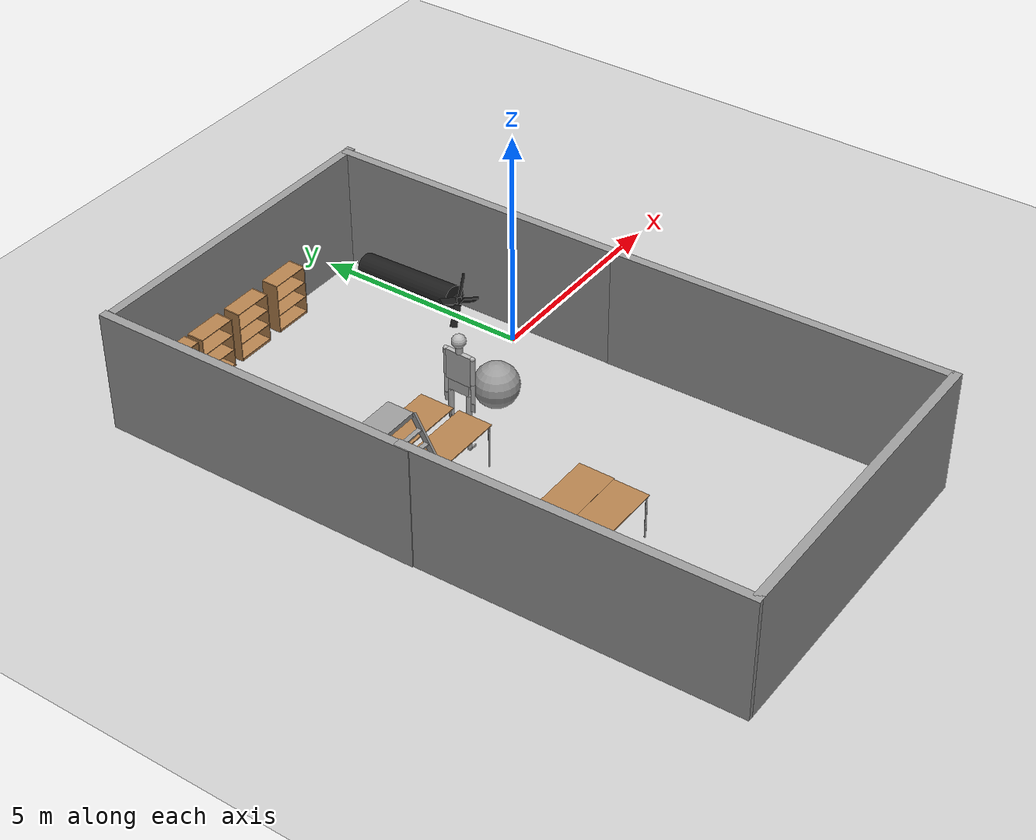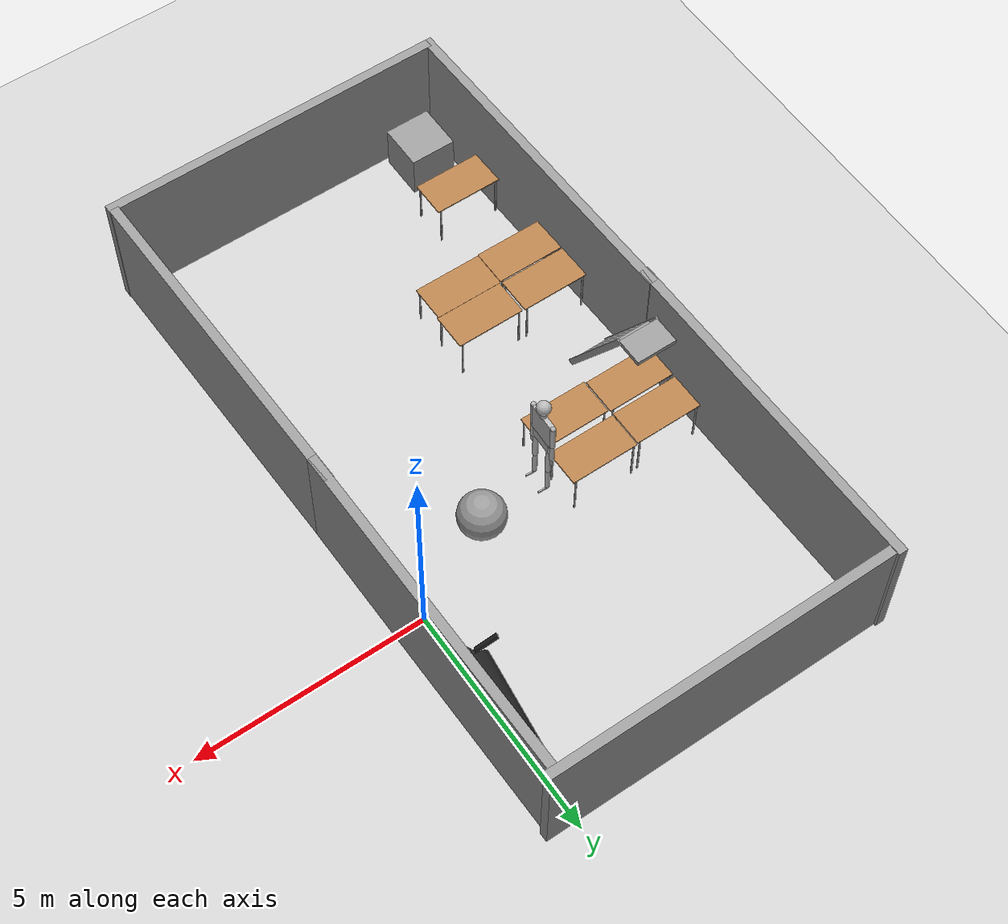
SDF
<sdf version="1.6">
 <world name="default">
  <light name="sun" type="directional">
   <pose>0 0 10 0 -0 0</pose>
   <diffuse>0.8 0.8 0.8 1</diffuse>
   <specular>0.2 0.2 0.2 1</specular>
   <attenuation>
    <range>1000</range>
    <constant>0.9</constant>
    <linear>0.01</linear>
    <quadratic>0.001</quadratic>
   </attenuation>
   <direction>-0.5 0.1 -0.9</direction>
  </light>
  <model name="ground_plane">
   <static>1</static>
   <link name="link">
    <collision name="collision">
     <geometry><plane><normal>0 0 1</normal><size>100 100</size></plane></geometry>
     <surface>
      <contact><collide_bitmask>65535</collide_bitmask></contact>
      <friction><ode><mu>100</mu><mu2>50</mu2></ode></friction>
     </surface>
    </collision>
    <visual name="visual">
     <cast_shadows>0</cast_shadows>
     <geometry><plane><normal>0 0 1</normal><size>100 100</size></plane></geometry>
     <material>
      <script><uri>file://media/materials/scripts/gazebo.material</uri><name>Gazebo/Grey</name></script>
     </material>
    </visual>
   </link>
  </model>
  <gravity>0 0 -9.8</gravity>
  <magnetic_field>6e-06 2.3e-05 -4.2e-05</magnetic_field>
  <atmosphere type="adiabatic"/>
  <physics name="default_physics" default="0" type="ode">
   <max_step_size>0.001</max_step_size>
   <real_time_factor>1</real_time_factor>
   <real_time_update_rate>1000</real_time_update_rate>
  </physics>
  <scene><ambient>0.4 0.4 0.4 1</ambient><background>0.7 0.7 0.7 1</background><shadows>1</shadows></scene>
  <spherical_coordinates>
   <surface_model>EARTH_WGS84</surface_model>
   <latitude_deg>0</latitude_deg>
   <longitude_deg>0</longitude_deg>
   <elevation>0</elevation>
   <heading_deg>0</heading_deg>
  </spherical_coordinates>
  <model name="grey_wall">
   <static>1</static>
   <link name="link">
    <pose>0 0 1.4 0 -0 0</pose>
    <collision name="collision"><geometry><box><size>7.5 0.2 2.8</size></box></geometry></collision>
    <visual name="visual">
     <cast_shadows>0</cast_shadows>
     <geometry><box><size>7.5 0.2 2.8</size></box></geometry>
     <material>
      <script>
       <uri>model://grey_wall/materials/scripts</uri>
       <uri>model://grey_wall/materials/textures</uri>
       <name>vrc/grey_wall</name>
      </script>
     </material>
    </visual>
   </link>
   <pose>-3.09863 4.75132 0 0 -0 0</pose>
  </model>
  <model name="grey_wall_0">
   <static>1</static>
   <link name="link">
    <pose>0 0 1.4 0 -0 0</pose>
    <collision name="collision"><geometry><box><size>7.5 0.2 2.8</size></box></geometry></collision>
    <visual name="visual">
     <cast_shadows>0</cast_shadows>
     <geometry><box><size>7.5 0.2 2.8</size></box></geometry>
     <material>
      <script>
       <uri>model://grey_wall/materials/scripts</uri>
       <uri>model://grey_wall/materials/textures</uri>
       <name>vrc/grey_wall</name>
      </script>
     </material>
    </visual>
   </link>
   <pose>-6.9051 1.14817 0 0 0 -1.55661</pose>
  </model>
  <model name="grey_wall_1">
   <static>1</static>
   <link name="link">
    <pose>0 0 1.4 0 -0 0</pose>
    <collision name="collision"><geometry><box><size>7.5 0.2 2.8</size></box></geometry></collision>
    <visual name="visual">
     <cast_shadows>0</cast_shadows>
     <geometry><box><size>7.5 0.2 2.8</size></box></geometry>
     <material>
      <script>
       <uri>model://grey_wall/materials/scripts</uri>
       <uri>model://grey_wall/materials/textures</uri>
       <name>vrc/grey_wall</name>
      </script>
     </material>
    </visual>
   </link>
   <pose>-6.7445 -6.00375 0 0 0 -1.546</pose>
  </model>
  <model name="grey_wall_2">
   <static>1</static>
   <link name="link">
    <pose>0 0 1.4 0 -0 0</pose>
    <collision name="collision"><geometry><box><size>7.5 0.2 2.8</size></box></geometry></collision>
    <visual name="visual">
     <cast_shadows>0</cast_shadows>
     <geometry><box><size>7.5 0.2 2.8</size></box></geometry>
     <material>
      <script>
       <uri>model://grey_wall/materials/scripts</uri>
       <uri>model://grey_wall/materials/textures</uri>
       <name>vrc/grey_wall</name>
      </script>
     </material>
    </visual>
   </link>
   <pose>-2.89104 -9.65366 0 0 -0 0</pose>
  </model>
  <model name="grey_wall_1_clone">
   <static>1</static>
   <link name="link">
    <pose>0 0 1.4 0 -0 0</pose>
    <collision name="collision"><geometry><box><size>7.5 0.2 2.8</size></box></geometry></collision>
    <visual name="visual">
     <cast_shadows>0</cast_shadows>
     <geometry><box><size>7.5 0.2 2.8</size></box></geometry>
     <material>
      <script>
       <uri>model://grey_wall/materials/scripts</uri>
       <uri>model://grey_wall/materials/textures</uri>
       <name>vrc/grey_wall</name>
      </script>
     </material>
    </visual>
   </link>
   <pose>0.654584 -5.8564 0 0 0 -1.546</pose>
  </model>
  <model name="grey_wall_0_clone">
   <static>1</static>
   <link name="link">
    <pose>0 0 1.4 0 -0 0</pose>
    <collision name="collision"><geometry><box><size>7.5 0.2 2.8</size></box></geometry></collision>
    <visual name="visual">
     <cast_shadows>0</cast_shadows>
     <geometry><box><size>7.5 0.2 2.8</size></box></geometry>
     <material>
      <script>
       <uri>model://grey_wall/materials/scripts</uri>
       <uri>model://grey_wall/materials/textures</uri>
       <name>vrc/grey_wall</name>
      </script>
     </material>
    </visual>
   </link>
   <pose>0.526199 1.0684 0 0 0 -1.55661</pose>
  </model>
  <model name="table_0">
   <static>1</static>
   <link name="link">
    <collision name="surface">
     <pose>0 0 1 0 -0 0</pose>
     <geometry><box><size>1.5 0.8 0.03</size></box></geometry>
     <surface><friction><ode><mu>0.6</mu><mu2>0.6</mu2></ode></friction></surface>
    </collision>
    <visual name="visual1">
     <pose>0 0 1 0 -0 0</pose>
     <geometry><box><size>1.5 0.8 0.03</size></box></geometry>
     <material>
      <script><uri>file://media/materials/scripts/gazebo.material</uri><name>Gazebo/Wood</name></script>
     </material>
    </visual>
    <collision name="front_left_leg">
     <pose>0.68 0.38 0.5 0 -0 0</pose>
     <geometry><cylinder><radius>0.02</radius><length>1</length></cylinder></geometry>
    </collision>
    <visual name="front_left_leg">
     <pose>0.68 0.38 0.5 0 -0 0</pose>
     <geometry><cylinder><radius>0.02</radius><length>1</length></cylinder></geometry>
     <material>
      <script><uri>file://media/materials/scripts/gazebo.material</uri><name>Gazebo/Grey</name></script>
     </material>
    </visual>
    <collision name="front_right_leg">
     <pose>0.68 -0.38 0.5 0 -0 0</pose>
     <geometry><cylinder><radius>0.02</radius><length>1</length></cylinder></geometry>
    </collision>
    <visual name="front_right_leg">
     <pose>0.68 -0.38 0.5 0 -0 0</pose>
     <geometry><cylinder><radius>0.02</radius><length>1</length></cylinder></geometry>
     <material>
      <script><uri>file://media/materials/scripts/gazebo.material</uri><name>Gazebo/Grey</name></script>
     </material>
    </visual>
    <collision name="back_right_leg">
     <pose>-0.68 -0.38 0.5 0 -0 0</pose>
     <geometry><cylinder><radius>0.02</radius><length>1</length></cylinder></geometry>
    </collision>
    <visual name="back_right_leg">
     <pose>-0.68 -0.38 0.5 0 -0 0</pose>
     <geometry><cylinder><radius>0.02</radius><length>1</length></cylinder></geometry>
     <material>
      <script><uri>file://media/materials/scripts/gazebo.material</uri><name>Gazebo/Grey</name></script>
     </material>
    </visual>
    <collision name="back_left_leg">
     <pose>-0.68 0.38 0.5 0 -0 0</pose>
     <geometry><cylinder><radius>0.02</radius><length>1</length></cylinder></geometry>
    </collision>
    <visual name="back_left_leg">
     <pose>-0.68 0.38 0.5 0 -0 0</pose>
     <geometry><cylinder><radius>0.02</radius><length>1</length></cylinder></geometry>
     <material>
      <script><uri>file://media/materials/scripts/gazebo.material</uri><name>Gazebo/Grey</name></script>
     </material>
    </visual>
   </link>
   <pose>-5.8711 -7.48729 0 0 -0 0</pose>
  </model>
  <model name="table_1">
   <static>1</static>
   <link name="link">
    <collision name="surface">
     <pose>0 0 1 0 -0 0</pose>
     <geometry><box><size>1.5 0.8 0.03</size></box></geometry>
     <surface><friction><ode><mu>0.6</mu><mu2>0.6</mu2></ode></friction></surface>
    </collision>
    <visual name="visual1">
     <pose>0 0 1 0 -0 0</pose>
     <geometry><box><size>1.5 0.8 0.03</size></box></geometry>
     <material>
      <script><uri>file://media/materials/scripts/gazebo.material</uri><name>Gazebo/Wood</name></script>
     </material>
    </visual>
    <collision name="front_left_leg">
     <pose>0.68 0.38 0.5 0 -0 0</pose>
     <geometry><cylinder><radius>0.02</radius><length>1</length></cylinder></geometry>
    </collision>
    <visual name="front_left_leg">
     <pose>0.68 0.38 0.5 0 -0 0</pose>
     <geometry><cylinder><radius>0.02</radius><length>1</length></cylinder></geometry>
     <material>
      <script><uri>file://media/materials/scripts/gazebo.material</uri><name>Gazebo/Grey</name></script>
     </material>
    </visual>
    <collision name="front_right_leg">
     <pose>0.68 -0.38 0.5 0 -0 0</pose>
     <geometry><cylinder><radius>0.02</radius><length>1</length></cylinder></geometry>
    </collision>
    <visual name="front_right_leg">
     <pose>0.68 -0.38 0.5 0 -0 0</pose>
     <geometry><cylinder><radius>0.02</radius><length>1</length></cylinder></geometry>
     <material>
      <script><uri>file://media/materials/scripts/gazebo.material</uri><name>Gazebo/Grey</name></script>
     </material>
    </visual>
    <collision name="back_right_leg">
     <pose>-0.68 -0.38 0.5 0 -0 0</pose>
     <geometry><cylinder><radius>0.02</radius><length>1</length></cylinder></geometry>
    </collision>
    <visual name="back_right_leg">
     <pose>-0.68 -0.38 0.5 0 -0 0</pose>
     <geometry><cylinder><radius>0.02</radius><length>1</length></cylinder></geometry>
     <material>
      <script><uri>file://media/materials/scripts/gazebo.material</uri><name>Gazebo/Grey</name></script>
     </material>
    </visual>
    <collision name="back_left_leg">
     <pose>-0.68 0.38 0.5 0 -0 0</pose>
     <geometry><cylinder><radius>0.02</radius><length>1</length></cylinder></geometry>
    </collision>
    <visual name="back_left_leg">
     <pose>-0.68 0.38 0.5 0 -0 0</pose>
     <geometry><cylinder><radius>0.02</radius><length>1</length></cylinder></geometry>
     <material>
      <script><uri>file://media/materials/scripts/gazebo.material</uri><name>Gazebo/Grey</name></script>
     </material>
    </visual>
   </link>
   <pose>-5.92304 -5.35107 0 0 -0 0</pose>
  </model>
  <model name="table_2">
   <static>1</static>
   <link name="link">
    <collision name="surface">
     <pose>0 0 1 0 -0 0</pose>
     <geometry><box><size>1.5 0.8 0.03</size></box></geometry>
     <surface><friction><ode><mu>0.6</mu><mu2>0.6</mu2></ode></friction></surface>
    </collision>
    <visual name="visual1">
     <pose>0 0 1 0 -0 0</pose>
     <geometry><box><size>1.5 0.8 0.03</size></box></geometry>
     <material>
      <script><uri>file://media/materials/scripts/gazebo.material</uri><name>Gazebo/Wood</name></script>
     </material>
    </visual>
    <collision name="front_left_leg">
     <pose>0.68 0.38 0.5 0 -0 0</pose>
     <geometry><cylinder><radius>0.02</radius><length>1</length></cylinder></geometry>
    </collision>
    <visual name="front_left_leg">
     <pose>0.68 0.38 0.5 0 -0 0</pose>
     <geometry><cylinder><radius>0.02</radius><length>1</length></cylinder></geometry>
     <material>
      <script><uri>file://media/materials/scripts/gazebo.material</uri><name>Gazebo/Grey</name></script>
     </material>
    </visual>
    <collision name="front_right_leg">
     <pose>0.68 -0.38 0.5 0 -0 0</pose>
     <geometry><cylinder><radius>0.02</radius><length>1</length></cylinder></geometry>
    </collision>
    <visual name="front_right_leg">
     <pose>0.68 -0.38 0.5 0 -0 0</pose>
     <geometry><cylinder><radius>0.02</radius><length>1</length></cylinder></geometry>
     <material>
      <script><uri>file://media/materials/scripts/gazebo.material</uri><name>Gazebo/Grey</name></script>
     </material>
    </visual>
    <collision name="back_right_leg">
     <pose>-0.68 -0.38 0.5 0 -0 0</pose>
     <geometry><cylinder><radius>0.02</radius><length>1</length></cylinder></geometry>
    </collision>
    <visual name="back_right_leg">
     <pose>-0.68 -0.38 0.5 0 -0 0</pose>
     <geometry><cylinder><radius>0.02</radius><length>1</length></cylinder></geometry>
     <material>
      <script><uri>file://media/materials/scripts/gazebo.material</uri><name>Gazebo/Grey</name></script>
     </material>
    </visual>
    <collision name="back_left_leg">
     <pose>-0.68 0.38 0.5 0 -0 0</pose>
     <geometry><cylinder><radius>0.02</radius><length>1</length></cylinder></geometry>
    </collision>
    <visual name="back_left_leg">
     <pose>-0.68 0.38 0.5 0 -0 0</pose>
     <geometry><cylinder><radius>0.02</radius><length>1</length></cylinder></geometry>
     <material>
      <script><uri>file://media/materials/scripts/gazebo.material</uri><name>Gazebo/Grey</name></script>
     </material>
    </visual>
   </link>
   <pose>-5.93597 -4.5163 0 0 -0 0</pose>
  </model>
  <model name="table_3">
   <static>1</static>
   <link name="link">
    <collision name="surface">
     <pose>0 0 1 0 -0 0</pose>
     <geometry><box><size>1.5 0.8 0.03</size></box></geometry>
     <surface><friction><ode><mu>0.6</mu><mu2>0.6</mu2></ode></friction></surface>
    </collision>
    <visual name="visual1">
     <pose>0 0 1 0 -0 0</pose>
     <geometry><box><size>1.5 0.8 0.03</size></box></geometry>
     <material>
      <script><uri>file://media/materials/scripts/gazebo.material</uri><name>Gazebo/Wood</name></script>
     </material>
    </visual>
    <collision name="front_left_leg">
     <pose>0.68 0.38 0.5 0 -0 0</pose>
     <geometry><cylinder><radius>0.02</radius><length>1</length></cylinder></geometry>
    </collision>
    <visual name="front_left_leg">
     <pose>0.68 0.38 0.5 0 -0 0</pose>
     <geometry><cylinder><radius>0.02</radius><length>1</length></cylinder></geometry>
     <material>
      <script><uri>file://media/materials/scripts/gazebo.material</uri><name>Gazebo/Grey</name></script>
     </material>
    </visual>
    <collision name="front_right_leg">
     <pose>0.68 -0.38 0.5 0 -0 0</pose>
     <geometry><cylinder><radius>0.02</radius><length>1</length></cylinder></geometry>
    </collision>
    <visual name="front_right_leg">
     <pose>0.68 -0.38 0.5 0 -0 0</pose>
     <geometry><cylinder><radius>0.02</radius><length>1</length></cylinder></geometry>
     <material>
      <script><uri>file://media/materials/scripts/gazebo.material</uri><name>Gazebo/Grey</name></script>
     </material>
    </visual>
    <collision name="back_right_leg">
     <pose>-0.68 -0.38 0.5 0 -0 0</pose>
     <geometry><cylinder><radius>0.02</radius><length>1</length></cylinder></geometry>
    </collision>
    <visual name="back_right_leg">
     <pose>-0.68 -0.38 0.5 0 -0 0</pose>
     <geometry><cylinder><radius>0.02</radius><length>1</length></cylinder></geometry>
     <material>
      <script><uri>file://media/materials/scripts/gazebo.material</uri><name>Gazebo/Grey</name></script>
     </material>
    </visual>
    <collision name="back_left_leg">
     <pose>-0.68 0.38 0.5 0 -0 0</pose>
     <geometry><cylinder><radius>0.02</radius><length>1</length></cylinder></geometry>
    </collision>
    <visual name="back_left_leg">
     <pose>-0.68 0.38 0.5 0 -0 0</pose>
     <geometry><cylinder><radius>0.02</radius><length>1</length></cylinder></geometry>
     <material>
      <script><uri>file://media/materials/scripts/gazebo.material</uri><name>Gazebo/Grey</name></script>
     </material>
    </visual>
   </link>
   <pose>-4.41713 -5.33099 0 0 -0 0</pose>
  </model>
  <model name="table_4">
   <static>1</static>
   <link name="link">
    <collision name="surface">
     <pose>0 0 1 0 -0 0</pose>
     <geometry><box><size>1.5 0.8 0.03</size></box></geometry>
     <surface><friction><ode><mu>0.6</mu><mu2>0.6</mu2></ode></friction></surface>
    </collision>
    <visual name="visual1">
     <pose>0 0 1 0 -0 0</pose>
     <geometry><box><size>1.5 0.8 0.03</size></box></geometry>
     <material>
      <script><uri>file://media/materials/scripts/gazebo.material</uri><name>Gazebo/Wood</name></script>
     </material>
    </visual>
    <collision name="front_left_leg">
     <pose>0.68 0.38 0.5 0 -0 0</pose>
     <geometry><cylinder><radius>0.02</radius><length>1</length></cylinder></geometry>
    </collision>
    <visual name="front_left_leg">
     <pose>0.68 0.38 0.5 0 -0 0</pose>
     <geometry><cylinder><radius>0.02</radius><length>1</length></cylinder></geometry>
     <material>
      <script><uri>file://media/materials/scripts/gazebo.material</uri><name>Gazebo/Grey</name></script>
     </material>
    </visual>
    <collision name="front_right_leg">
     <pose>0.68 -0.38 0.5 0 -0 0</pose>
     <geometry><cylinder><radius>0.02</radius><length>1</length></cylinder></geometry>
    </collision>
    <visual name="front_right_leg">
     <pose>0.68 -0.38 0.5 0 -0 0</pose>
     <geometry><cylinder><radius>0.02</radius><length>1</length></cylinder></geometry>
     <material>
      <script><uri>file://media/materials/scripts/gazebo.material</uri><name>Gazebo/Grey</name></script>
     </material>
    </visual>
    <collision name="back_right_leg">
     <pose>-0.68 -0.38 0.5 0 -0 0</pose>
     <geometry><cylinder><radius>0.02</radius><length>1</length></cylinder></geometry>
    </collision>
    <visual name="back_right_leg">
     <pose>-0.68 -0.38 0.5 0 -0 0</pose>
     <geometry><cylinder><radius>0.02</radius><length>1</length></cylinder></geometry>
     <material>
      <script><uri>file://media/materials/scripts/gazebo.material</uri><name>Gazebo/Grey</name></script>
     </material>
    </visual>
    <collision name="back_left_leg">
     <pose>-0.68 0.38 0.5 0 -0 0</pose>
     <geometry><cylinder><radius>0.02</radius><length>1</length></cylinder></geometry>
    </collision>
    <visual name="back_left_leg">
     <pose>-0.68 0.38 0.5 0 -0 0</pose>
     <geometry><cylinder><radius>0.02</radius><length>1</length></cylinder></geometry>
     <material>
      <script><uri>file://media/materials/scripts/gazebo.material</uri><name>Gazebo/Grey</name></script>
     </material>
    </visual>
   </link>
   <pose>-4.38813 -4.52745 0 0 -0 0</pose>
  </model>
  <model name="table_7">
   <static>1</static>
   <link name="link">
    <collision name="surface">
     <pose>0 0 1 0 -0 0</pose>
     <geometry><box><size>1.5 0.8 0.03</size></box></geometry>
     <surface><friction><ode><mu>0.6</mu><mu2>0.6</mu2></ode></friction></surface>
    </collision>
    <visual name="visual1">
     <pose>0 0 1 0 -0 0</pose>
     <geometry><box><size>1.5 0.8 0.03</size></box></geometry>
     <material>
      <script><uri>file://media/materials/scripts/gazebo.material</uri><name>Gazebo/Wood</name></script>
     </material>
    </visual>
    <collision name="front_left_leg">
     <pose>0.68 0.38 0.5 0 -0 0</pose>
     <geometry><cylinder><radius>0.02</radius><length>1</length></cylinder></geometry>
    </collision>
    <visual name="front_left_leg">
     <pose>0.68 0.38 0.5 0 -0 0</pose>
     <geometry><cylinder><radius>0.02</radius><length>1</length></cylinder></geometry>
     <material>
      <script><uri>file://media/materials/scripts/gazebo.material</uri><name>Gazebo/Grey</name></script>
     </material>
    </visual>
    <collision name="front_right_leg">
     <pose>0.68 -0.38 0.5 0 -0 0</pose>
     <geometry><cylinder><radius>0.02</radius><length>1</length></cylinder></geometry>
    </collision>
    <visual name="front_right_leg">
     <pose>0.68 -0.38 0.5 0 -0 0</pose>
     <geometry><cylinder><radius>0.02</radius><length>1</length></cylinder></geometry>
     <material>
      <script><uri>file://media/materials/scripts/gazebo.material</uri><name>Gazebo/Grey</name></script>
     </material>
    </visual>
    <collision name="back_right_leg">
     <pose>-0.68 -0.38 0.5 0 -0 0</pose>
     <geometry><cylinder><radius>0.02</radius><length>1</length></cylinder></geometry>
    </collision>
    <visual name="back_right_leg">
     <pose>-0.68 -0.38 0.5 0 -0 0</pose>
     <geometry><cylinder><radius>0.02</radius><length>1</length></cylinder></geometry>
     <material>
      <script><uri>file://media/materials/scripts/gazebo.material</uri><name>Gazebo/Grey</name></script>
     </material>
    </visual>
    <collision name="back_left_leg">
     <pose>-0.68 0.38 0.5 0 -0 0</pose>
     <geometry><cylinder><radius>0.02</radius><length>1</length></cylinder></geometry>
    </collision>
    <visual name="back_left_leg">
     <pose>-0.68 0.38 0.5 0 -0 0</pose>
     <geometry><cylinder><radius>0.02</radius><length>1</length></cylinder></geometry>
     <material>
      <script><uri>file://media/materials/scripts/gazebo.material</uri><name>Gazebo/Grey</name></script>
     </material>
    </visual>
   </link>
   <pose>-5.9259 -1.63767 0 0 -0 0</pose>
  </model>
  <model name="table_8">
   <static>1</static>
   <link name="link">
    <collision name="surface">
     <pose>0 0 1 0 -0 0</pose>
     <geometry><box><size>1.5 0.8 0.03</size></box></geometry>
     <surface><friction><ode><mu>0.6</mu><mu2>0.6</mu2></ode></friction></surface>
    </collision>
    <visual name="visual1">
     <pose>0 0 1 0 -0 0</pose>
     <geometry><box><size>1.5 0.8 0.03</size></box></geometry>
     <material>
      <script><uri>file://media/materials/scripts/gazebo.material</uri><name>Gazebo/Wood</name></script>
     </material>
    </visual>
    <collision name="front_left_leg">
     <pose>0.68 0.38 0.5 0 -0 0</pose>
     <geometry><cylinder><radius>0.02</radius><length>1</length></cylinder></geometry>
    </collision>
    <visual name="front_left_leg">
     <pose>0.68 0.38 0.5 0 -0 0</pose>
     <geometry><cylinder><radius>0.02</radius><length>1</length></cylinder></geometry>
     <material>
      <script><uri>file://media/materials/scripts/gazebo.material</uri><name>Gazebo/Grey</name></script>
     </material>
    </visual>
    <collision name="front_right_leg">
     <pose>0.68 -0.38 0.5 0 -0 0</pose>
     <geometry><cylinder><radius>0.02</radius><length>1</length></cylinder></geometry>
    </collision>
    <visual name="front_right_leg">
     <pose>0.68 -0.38 0.5 0 -0 0</pose>
     <geometry><cylinder><radius>0.02</radius><length>1</length></cylinder></geometry>
     <material>
      <script><uri>file://media/materials/scripts/gazebo.material</uri><name>Gazebo/Grey</name></script>
     </material>
    </visual>
    <collision name="back_right_leg">
     <pose>-0.68 -0.38 0.5 0 -0 0</pose>
     <geometry><cylinder><radius>0.02</radius><length>1</length></cylinder></geometry>
    </collision>
    <visual name="back_right_leg">
     <pose>-0.68 -0.38 0.5 0 -0 0</pose>
     <geometry><cylinder><radius>0.02</radius><length>1</length></cylinder></geometry>
     <material>
      <script><uri>file://media/materials/scripts/gazebo.material</uri><name>Gazebo/Grey</name></script>
     </material>
    </visual>
    <collision name="back_left_leg">
     <pose>-0.68 0.38 0.5 0 -0 0</pose>
     <geometry><cylinder><radius>0.02</radius><length>1</length></cylinder></geometry>
    </collision>
    <visual name="back_left_leg">
     <pose>-0.68 0.38 0.5 0 -0 0</pose>
     <geometry><cylinder><radius>0.02</radius><length>1</length></cylinder></geometry>
     <material>
      <script><uri>file://media/materials/scripts/gazebo.material</uri><name>Gazebo/Grey</name></script>
     </material>
    </visual>
   </link>
   <pose>-5.92661 -0.763536 0 0 -0 0</pose>
  </model>
  <model name="table_9">
   <static>1</static>
   <link name="link">
    <collision name="surface">
     <pose>0 0 1 0 -0 0</pose>
     <geometry><box><size>1.5 0.8 0.03</size></box></geometry>
     <surface><friction><ode><mu>0.6</mu><mu2>0.6</mu2></ode></friction></surface>
    </collision>
    <visual name="visual1">
     <pose>0 0 1 0 -0 0</pose>
     <geometry><box><size>1.5 0.8 0.03</size></box></geometry>
     <material>
      <script><uri>file://media/materials/scripts/gazebo.material</uri><name>Gazebo/Wood</name></script>
     </material>
    </visual>
    <collision name="front_left_leg">
     <pose>0.68 0.38 0.5 0 -0 0</pose>
     <geometry><cylinder><radius>0.02</radius><length>1</length></cylinder></geometry>
    </collision>
    <visual name="front_left_leg">
     <pose>0.68 0.38 0.5 0 -0 0</pose>
     <geometry><cylinder><radius>0.02</radius><length>1</length></cylinder></geometry>
     <material>
      <script><uri>file://media/materials/scripts/gazebo.material</uri><name>Gazebo/Grey</name></script>
     </material>
    </visual>
    <collision name="front_right_leg">
     <pose>0.68 -0.38 0.5 0 -0 0</pose>
     <geometry><cylinder><radius>0.02</radius><length>1</length></cylinder></geometry>
    </collision>
    <visual name="front_right_leg">
     <pose>0.68 -0.38 0.5 0 -0 0</pose>
     <geometry><cylinder><radius>0.02</radius><length>1</length></cylinder></geometry>
     <material>
      <script><uri>file://media/materials/scripts/gazebo.material</uri><name>Gazebo/Grey</name></script>
     </material>
    </visual>
    <collision name="back_right_leg">
     <pose>-0.68 -0.38 0.5 0 -0 0</pose>
     <geometry><cylinder><radius>0.02</radius><length>1</length></cylinder></geometry>
    </collision>
    <visual name="back_right_leg">
     <pose>-0.68 -0.38 0.5 0 -0 0</pose>
     <geometry><cylinder><radius>0.02</radius><length>1</length></cylinder></geometry>
     <material>
      <script><uri>file://media/materials/scripts/gazebo.material</uri><name>Gazebo/Grey</name></script>
     </material>
    </visual>
    <collision name="back_left_leg">
     <pose>-0.68 0.38 0.5 0 -0 0</pose>
     <geometry><cylinder><radius>0.02</radius><length>1</length></cylinder></geometry>
    </collision>
    <visual name="back_left_leg">
     <pose>-0.68 0.38 0.5 0 -0 0</pose>
     <geometry><cylinder><radius>0.02</radius><length>1</length></cylinder></geometry>
     <material>
      <script><uri>file://media/materials/scripts/gazebo.material</uri><name>Gazebo/Grey</name></script>
     </material>
    </visual>
   </link>
   <pose>-4.3962 -1.67397 0 0 -0 0</pose>
  </model>
  <model name="table_10">
   <static>1</static>
   <link name="link">
    <collision name="surface">
     <pose>0 0 1 0 -0 0</pose>
     <geometry><box><size>1.5 0.8 0.03</size></box></geometry>
     <surface><friction><ode><mu>0.6</mu><mu2>0.6</mu2></ode></friction></surface>
    </collision>
    <visual name="visual1">
     <pose>0 0 1 0 -0 0</pose>
     <geometry><box><size>1.5 0.8 0.03</size></box></geometry>
     <material>
      <script><uri>file://media/materials/scripts/gazebo.material</uri><name>Gazebo/Wood</name></script>
     </material>
    </visual>
    <collision name="front_left_leg">
     <pose>0.68 0.38 0.5 0 -0 0</pose>
     <geometry><cylinder><radius>0.02</radius><length>1</length></cylinder></geometry>
    </collision>
    <visual name="front_left_leg">
     <pose>0.68 0.38 0.5 0 -0 0</pose>
     <geometry><cylinder><radius>0.02</radius><length>1</length></cylinder></geometry>
     <material>
      <script><uri>file://media/materials/scripts/gazebo.material</uri><name>Gazebo/Grey</name></script>
     </material>
    </visual>
    <collision name="front_right_leg">
     <pose>0.68 -0.38 0.5 0 -0 0</pose>
     <geometry><cylinder><radius>0.02</radius><length>1</length></cylinder></geometry>
    </collision>
    <visual name="front_right_leg">
     <pose>0.68 -0.38 0.5 0 -0 0</pose>
     <geometry><cylinder><radius>0.02</radius><length>1</length></cylinder></geometry>
     <material>
      <script><uri>file://media/materials/scripts/gazebo.material</uri><name>Gazebo/Grey</name></script>
     </material>
    </visual>
    <collision name="back_right_leg">
     <pose>-0.68 -0.38 0.5 0 -0 0</pose>
     <geometry><cylinder><radius>0.02</radius><length>1</length></cylinder></geometry>
    </collision>
    <visual name="back_right_leg">
     <pose>-0.68 -0.38 0.5 0 -0 0</pose>
     <geometry><cylinder><radius>0.02</radius><length>1</length></cylinder></geometry>
     <material>
      <script><uri>file://media/materials/scripts/gazebo.material</uri><name>Gazebo/Grey</name></script>
     </material>
    </visual>
    <collision name="back_left_leg">
     <pose>-0.68 0.38 0.5 0 -0 0</pose>
     <geometry><cylinder><radius>0.02</radius><length>1</length></cylinder></geometry>
    </collision>
    <visual name="back_left_leg">
     <pose>-0.68 0.38 0.5 0 -0 0</pose>
     <geometry><cylinder><radius>0.02</radius><length>1</length></cylinder></geometry>
     <material>
      <script><uri>file://media/materials/scripts/gazebo.material</uri><name>Gazebo/Grey</name></script>
     </material>
    </visual>
   </link>
   <pose>-4.40357 -0.743529 0 0 -0 0</pose>
  </model>
  <model name="bookshelf">
   <static>1</static>
   <link name="link">
    <inertial><mass>1</mass></inertial>
    <collision name="back">
     <pose>0 0.005 0.6 0 -0 0</pose>
     <geometry><box><size>0.9 0.01 1.2</size></box></geometry>
    </collision>
    <visual name="visual1">
     <pose>0 0.005 0.6 0 -0 0</pose>
     <geometry><box><size>0.9 0.01 1.2</size></box></geometry>
     <material>
      <script><uri>file://media/materials/scripts/gazebo.material</uri><name>Gazebo/Wood</name></script>
     </material>
    </visual>
    <collision name="left_side">
     <pose>0.45 -0.195 0.6 0 -0 0</pose>
     <geometry><box><size>0.02 0.4 1.2</size></box></geometry>
    </collision>
    <visual name="visual2">
     <pose>0.45 -0.195 0.6 0 -0 0</pose>
     <geometry><box><size>0.02 0.4 1.2</size></box></geometry>
     <material>
      <script><uri>file://media/materials/scripts/gazebo.material</uri><name>Gazebo/Wood</name></script>
     </material>
    </visual>
    <collision name="right_side">
     <pose>-0.45 -0.195 0.6 0 -0 0</pose>
     <geometry><box><size>0.02 0.4 1.2</size></box></geometry>
    </collision>
    <visual name="visual3">
     <pose>-0.45 -0.195 0.6 0 -0 0</pose>
     <geometry><box><size>0.02 0.4 1.2</size></box></geometry>
     <material>
      <script><uri>file://media/materials/scripts/gazebo.material</uri><name>Gazebo/Wood</name></script>
     </material>
    </visual>
    <collision name="bottom">
     <pose>0 -0.195 0.03 0 -0 0</pose>
     <geometry><box><size>0.88 0.4 0.06</size></box></geometry>
    </collision>
    <visual name="visual4">
     <pose>0 -0.195 0.03 0 -0 0</pose>
     <geometry><box><size>0.88 0.4 0.06</size></box></geometry>
     <material>
      <script><uri>file://media/materials/scripts/gazebo.material</uri><name>Gazebo/Wood</name></script>
     </material>
    </visual>
    <collision name="top">
     <pose>0 -0.195 1.19 0 -0 0</pose>
     <geometry><box><size>0.88 0.4 0.02</size></box></geometry>
    </collision>
    <visual name="visual5">
     <pose>0 -0.195 1.19 0 -0 0</pose>
     <geometry><box><size>0.88 0.4 0.02</size></box></geometry>
     <material>
      <script><uri>file://media/materials/scripts/gazebo.material</uri><name>Gazebo/Wood</name></script>
     </material>
    </visual>
    <collision name="low_shelf">
     <pose>0 -0.195 0.43 0 -0 0</pose>
     <geometry><box><size>0.88 0.4 0.02</size></box></geometry>
    </collision>
    <visual name="visual6">
     <pose>0 -0.195 0.43 0 -0 0</pose>
     <geometry><box><size>0.88 0.4 0.02</size></box></geometry>
     <material>
      <script><uri>file://media/materials/scripts/gazebo.material</uri><name>Gazebo/Wood</name></script>
     </material>
    </visual>
    <collision name="high_shelf">
     <pose>0 -0.195 0.8 0 -0 0</pose>
     <geometry><box><size>0.88 0.4 0.02</size></box></geometry>
    </collision>
    <visual name="visual7">
     <pose>0 -0.195 0.8 0 -0 0</pose>
     <geometry><box><size>0.88 0.4 0.02</size></box></geometry>
     <material>
      <script><uri>file://media/materials/scripts/gazebo.material</uri><name>Gazebo/Wood</name></script>
     </material>
    </visual>
   </link>
   <pose>-5.52954 4.67114 0 0 -0 0</pose>
  </model>
  <model name="bookshelf_0">
   <static>1</static>
   <link name="link">
    <inertial><mass>1</mass></inertial>
    <collision name="back">
     <pose>0 0.005 0.6 0 -0 0</pose>
     <geometry><box><size>0.9 0.01 1.2</size></box></geometry>
    </collision>
    <visual name="visual1">
     <pose>0 0.005 0.6 0 -0 0</pose>
     <geometry><box><size>0.9 0.01 1.2</size></box></geometry>
     <material>
      <script><uri>file://media/materials/scripts/gazebo.material</uri><name>Gazebo/Wood</name></script>
     </material>
    </visual>
    <collision name="left_side">
     <pose>0.45 -0.195 0.6 0 -0 0</pose>
     <geometry><box><size>0.02 0.4 1.2</size></box></geometry>
    </collision>
    <visual name="visual2">
     <pose>0.45 -0.195 0.6 0 -0 0</pose>
     <geometry><box><size>0.02 0.4 1.2</size></box></geometry>
     <material>
      <script><uri>file://media/materials/scripts/gazebo.material</uri><name>Gazebo/Wood</name></script>
     </material>
    </visual>
    <collision name="right_side">
     <pose>-0.45 -0.195 0.6 0 -0 0</pose>
     <geometry><box><size>0.02 0.4 1.2</size></box></geometry>
    </collision>
    <visual name="visual3">
     <pose>-0.45 -0.195 0.6 0 -0 0</pose>
     <geometry><box><size>0.02 0.4 1.2</size></box></geometry>
     <material>
      <script><uri>file://media/materials/scripts/gazebo.material</uri><name>Gazebo/Wood</name></script>
     </material>
    </visual>
    <collision name="bottom">
     <pose>0 -0.195 0.03 0 -0 0</pose>
     <geometry><box><size>0.88 0.4 0.06</size></box></geometry>
    </collision>
    <visual name="visual4">
     <pose>0 -0.195 0.03 0 -0 0</pose>
     <geometry><box><size>0.88 0.4 0.06</size></box></geometry>
     <material>
      <script><uri>file://media/materials/scripts/gazebo.material</uri><name>Gazebo/Wood</name></script>
     </material>
    </visual>
    <collision name="top">
     <pose>0 -0.195 1.19 0 -0 0</pose>
     <geometry><box><size>0.88 0.4 0.02</size></box></geometry>
    </collision>
    <visual name="visual5">
     <pose>0 -0.195 1.19 0 -0 0</pose>
     <geometry><box><size>0.88 0.4 0.02</size></box></geometry>
     <material>
      <script><uri>file://media/materials/scripts/gazebo.material</uri><name>Gazebo/Wood</name></script>
     </material>
    </visual>
    <collision name="low_shelf">
     <pose>0 -0.195 0.43 0 -0 0</pose>
     <geometry><box><size>0.88 0.4 0.02</size></box></geometry>
    </collision>
    <visual name="visual6">
     <pose>0 -0.195 0.43 0 -0 0</pose>
     <geometry><box><size>0.88 0.4 0.02</size></box></geometry>
     <material>
      <script><uri>file://media/materials/scripts/gazebo.material</uri><name>Gazebo/Wood</name></script>
     </material>
    </visual>
    <collision name="high_shelf">
     <pose>0 -0.195 0.8 0 -0 0</pose>
     <geometry><box><size>0.88 0.4 0.02</size></box></geometry>
    </collision>
    <visual name="visual7">
     <pose>0 -0.195 0.8 0 -0 0</pose>
     <geometry><box><size>0.88 0.4 0.02</size></box></geometry>
     <material>
      <script><uri>file://media/materials/scripts/gazebo.material</uri><name>Gazebo/Wood</name></script>
     </material>
    </visual>
   </link>
   <pose>-4.5447 4.63763 0 0 -0 0</pose>
  </model>
  <model name="bookshelf_1">
   <static>1</static>
   <link name="link">
    <inertial><mass>1</mass></inertial>
    <collision name="back">
     <pose>0 0.005 0.6 0 -0 0</pose>
     <geometry><box><size>0.9 0.01 1.2</size></box></geometry>
    </collision>
    <visual name="visual1">
     <pose>0 0.005 0.6 0 -0 0</pose>
     <geometry><box><size>0.9 0.01 1.2</size></box></geometry>
     <material>
      <script><uri>file://media/materials/scripts/gazebo.material</uri><name>Gazebo/Wood</name></script>
     </material>
    </visual>
    <collision name="left_side">
     <pose>0.45 -0.195 0.6 0 -0 0</pose>
     <geometry><box><size>0.02 0.4 1.2</size></box></geometry>
    </collision>
    <visual name="visual2">
     <pose>0.45 -0.195 0.6 0 -0 0</pose>
     <geometry><box><size>0.02 0.4 1.2</size></box></geometry>
     <material>
      <script><uri>file://media/materials/scripts/gazebo.material</uri><name>Gazebo/Wood</name></script>
     </material>
    </visual>
    <collision name="right_side">
     <pose>-0.45 -0.195 0.6 0 -0 0</pose>
     <geometry><box><size>0.02 0.4 1.2</size></box></geometry>
    </collision>
    <visual name="visual3">
     <pose>-0.45 -0.195 0.6 0 -0 0</pose>
     <geometry><box><size>0.02 0.4 1.2</size></box></geometry>
     <material>
      <script><uri>file://media/materials/scripts/gazebo.material</uri><name>Gazebo/Wood</name></script>
     </material>
    </visual>
    <collision name="bottom">
     <pose>0 -0.195 0.03 0 -0 0</pose>
     <geometry><box><size>0.88 0.4 0.06</size></box></geometry>
    </collision>
    <visual name="visual4">
     <pose>0 -0.195 0.03 0 -0 0</pose>
     <geometry><box><size>0.88 0.4 0.06</size></box></geometry>
     <material>
      <script><uri>file://media/materials/scripts/gazebo.material</uri><name>Gazebo/Wood</name></script>
     </material>
    </visual>
    <collision name="top">
     <pose>0 -0.195 1.19 0 -0 0</pose>
     <geometry><box><size>0.88 0.4 0.02</size></box></geometry>
    </collision>
    <visual name="visual5">
     <pose>0 -0.195 1.19 0 -0 0</pose>
     <geometry><box><size>0.88 0.4 0.02</size></box></geometry>
     <material>
      <script><uri>file://media/materials/scripts/gazebo.material</uri><name>Gazebo/Wood</name></script>
     </material>
    </visual>
    <collision name="low_shelf">
     <pose>0 -0.195 0.43 0 -0 0</pose>
     <geometry><box><size>0.88 0.4 0.02</size></box></geometry>
    </collision>
    <visual name="visual6">
     <pose>0 -0.195 0.43 0 -0 0</pose>
     <geometry><box><size>0.88 0.4 0.02</size></box></geometry>
     <material>
      <script><uri>file://media/materials/scripts/gazebo.material</uri><name>Gazebo/Wood</name></script>
     </material>
    </visual>
    <collision name="high_shelf">
     <pose>0 -0.195 0.8 0 -0 0</pose>
     <geometry><box><size>0.88 0.4 0.02</size></box></geometry>
    </collision>
    <visual name="visual7">
     <pose>0 -0.195 0.8 0 -0 0</pose>
     <geometry><box><size>0.88 0.4 0.02</size></box></geometry>
     <material>
      <script><uri>file://media/materials/scripts/gazebo.material</uri><name>Gazebo/Wood</name></script>
     </material>
    </visual>
   </link>
   <pose>-3.43568 4.62036 0 0 -0 0</pose>
  </model>
  <model name="bookshelf_2">
   <static>1</static>
   <link name="link">
    <inertial><mass>1</mass></inertial>
    <collision name="back">
     <pose>0 0.005 0.6 0 -0 0</pose>
     <geometry><box><size>0.9 0.01 1.2</size></box></geometry>
    </collision>
    <visual name="visual1">
     <pose>0 0.005 0.6 0 -0 0</pose>
     <geometry><box><size>0.9 0.01 1.2</size></box></geometry>
     <material>
      <script><uri>file://media/materials/scripts/gazebo.material</uri><name>Gazebo/Wood</name></script>
     </material>
    </visual>
    <collision name="left_side">
     <pose>0.45 -0.195 0.6 0 -0 0</pose>
     <geometry><box><size>0.02 0.4 1.2</size></box></geometry>
    </collision>
    <visual name="visual2">
     <pose>0.45 -0.195 0.6 0 -0 0</pose>
     <geometry><box><size>0.02 0.4 1.2</size></box></geometry>
     <material>
      <script><uri>file://media/materials/scripts/gazebo.material</uri><name>Gazebo/Wood</name></script>
     </material>
    </visual>
    <collision name="right_side">
     <pose>-0.45 -0.195 0.6 0 -0 0</pose>
     <geometry><box><size>0.02 0.4 1.2</size></box></geometry>
    </collision>
    <visual name="visual3">
     <pose>-0.45 -0.195 0.6 0 -0 0</pose>
     <geometry><box><size>0.02 0.4 1.2</size></box></geometry>
     <material>
      <script><uri>file://media/materials/scripts/gazebo.material</uri><name>Gazebo/Wood</name></script>
     </material>
    </visual>
    <collision name="bottom">
     <pose>0 -0.195 0.03 0 -0 0</pose>
     <geometry><box><size>0.88 0.4 0.06</size></box></geometry>
    </collision>
    <visual name="visual4">
     <pose>0 -0.195 0.03 0 -0 0</pose>
     <geometry><box><size>0.88 0.4 0.06</size></box></geometry>
     <material>
      <script><uri>file://media/materials/scripts/gazebo.material</uri><name>Gazebo/Wood</name></script>
     </material>
    </visual>
    <collision name="top">
     <pose>0 -0.195 1.19 0 -0 0</pose>
     <geometry><box><size>0.88 0.4 0.02</size></box></geometry>
    </collision>
    <visual name="visual5">
     <pose>0 -0.195 1.19 0 -0 0</pose>
     <geometry><box><size>0.88 0.4 0.02</size></box></geometry>
     <material>
      <script><uri>file://media/materials/scripts/gazebo.material</uri><name>Gazebo/Wood</name></script>
     </material>
    </visual>
    <collision name="low_shelf">
     <pose>0 -0.195 0.43 0 -0 0</pose>
     <geometry><box><size>0.88 0.4 0.02</size></box></geometry>
    </collision>
    <visual name="visual6">
     <pose>0 -0.195 0.43 0 -0 0</pose>
     <geometry><box><size>0.88 0.4 0.02</size></box></geometry>
     <material>
      <script><uri>file://media/materials/scripts/gazebo.material</uri><name>Gazebo/Wood</name></script>
     </material>
    </visual>
    <collision name="high_shelf">
     <pose>0 -0.195 0.8 0 -0 0</pose>
     <geometry><box><size>0.88 0.4 0.02</size></box></geometry>
    </collision>
    <visual name="visual7">
     <pose>0 -0.195 0.8 0 -0 0</pose>
     <geometry><box><size>0.88 0.4 0.02</size></box></geometry>
     <material>
      <script><uri>file://media/materials/scripts/gazebo.material</uri><name>Gazebo/Wood</name></script>
     </material>
    </visual>
   </link>
   <pose>-2.19279 4.63709 0 0 -0 0</pose>
  </model>
  <model name="ladder_60deg_0rails">
   <static>1</static>
   <link name="step0">
    <pose>0 0.15396 0.266667 0 -0 0</pose>
    <inertial>
     <mass>9.75482</mass>
     <inertia>
      <ixx>0.00957124</ixx>
      <iyy>0.65963</iyy>
      <izz>0.666842</izz>
      <ixy>0</ixy>
      <ixz>0</ixz>
      <iyz>0</iyz>
     </inertia>
    </inertial>
    <collision name="collision"><geometry><box><size>0.9 0.1016 0.0381</size></box></geometry></collision>
    <visual name="visual">
     <geometry><box><size>0.9 0.1016 0.0381</size></box></geometry>
     <material>
      <script><uri>file://media/materials/scripts/gazebo.material</uri><name>Gazebo/Grey</name></script>
     </material>
    </visual>
   </link>
   <link name="step1">
    <pose>0 0.30792 0.533333 0 -0 0</pose>
    <inertial>
     <mass>9.75482</mass>
     <inertia>
      <ixx>0.00957124</ixx>
      <iyy>0.65963</iyy>
      <izz>0.666842</izz>
      <ixy>0</ixy>
      <ixz>0</ixz>
      <iyz>0</iyz>
     </inertia>
    </inertial>
    <collision name="collision"><geometry><box><size>0.9 0.1016 0.0381</size></box></geometry></collision>
    <visual name="visual">
     <geometry><box><size>0.9 0.1016 0.0381</size></box></geometry>
     <material>
      <script><uri>file://media/materials/scripts/gazebo.material</uri><name>Gazebo/Grey</name></script>
     </material>
    </visual>
   </link>
   <link name="step2">
    <pose>0 0.46188 0.8 0 -0 0</pose>
    <inertial>
     <mass>9.75482</mass>
     <inertia>
      <ixx>0.00957124</ixx>
      <iyy>0.65963</iyy>
      <izz>0.666842</izz>
      <ixy>0</ixy>
      <ixz>0</ixz>
      <iyz>0</iyz>
     </inertia>
    </inertial>
    <collision name="collision"><geometry><box><size>0.9 0.1016 0.0381</size></box></geometry></collision>
    <visual name="visual">
     <geometry><box><size>0.9 0.1016 0.0381</size></box></geometry>
     <material>
      <script><uri>file://media/materials/scripts/gazebo.material</uri><name>Gazebo/Grey</name></script>
     </material>
    </visual>
   </link>
   <link name="step3">
    <pose>0 0.61584 1.06667 0 -0 0</pose>
    <inertial>
     <mass>9.75482</mass>
     <inertia>
      <ixx>0.00957124</ixx>
      <iyy>0.65963</iyy>
      <izz>0.666842</izz>
      <ixy>0</ixy>
      <ixz>0</ixz>
      <iyz>0</iyz>
     </inertia>
    </inertial>
    <collision name="collision"><geometry><box><size>0.9 0.1016 0.0381</size></box></geometry></collision>
    <visual name="visual">
     <geometry><box><size>0.9 0.1016 0.0381</size></box></geometry>
     <material>
      <script><uri>file://media/materials/scripts/gazebo.material</uri><name>Gazebo/Grey</name></script>
     </material>
    </visual>
   </link>
   <link name="step4">
    <pose>0 0.7698 1.33333 0 -0 0</pose>
    <inertial>
     <mass>9.75482</mass>
     <inertia>
      <ixx>0.00957124</ixx>
      <iyy>0.65963</iyy>
      <izz>0.666842</izz>
      <ixy>0</ixy>
      <ixz>0</ixz>
      <iyz>0</iyz>
     </inertia>
    </inertial>
    <collision name="collision"><geometry><box><size>0.9 0.1016 0.0381</size></box></geometry></collision>
    <visual name="visual">
     <geometry><box><size>0.9 0.1016 0.0381</size></box></geometry>
     <material>
      <script><uri>file://media/materials/scripts/gazebo.material</uri><name>Gazebo/Grey</name></script>
     </material>
    </visual>
   </link>
   <link name="step5">
    <pose>0 0.92376 1.6 0 -0 0</pose>
    <inertial>
     <mass>9.75482</mass>
     <inertia>
      <ixx>0.00957124</ixx>
      <iyy>0.65963</iyy>
      <izz>0.666842</izz>
      <ixy>0</ixy>
      <ixz>0</ixz>
      <iyz>0</iyz>
     </inertia>
    </inertial>
    <collision name="collision"><geometry><box><size>0.9 0.1016 0.0381</size></box></geometry></collision>
    <visual name="visual">
     <geometry><box><size>0.9 0.1016 0.0381</size></box></geometry>
     <material>
      <script><uri>file://media/materials/scripts/gazebo.material</uri><name>Gazebo/Grey</name></script>
     </material>
    </visual>
   </link>
   <link name="step6">
    <pose>0 1.07772 1.86667 0 -0 0</pose>
    <inertial>
     <mass>9.75482</mass>
     <inertia>
      <ixx>0.00957124</ixx>
      <iyy>0.65963</iyy>
      <izz>0.666842</izz>
      <ixy>0</ixy>
      <ixz>0</ixz>
      <iyz>0</iyz>
     </inertia>
    </inertial>
    <collision name="collision"><geometry><box><size>0.9 0.1016 0.0381</size></box></geometry></collision>
    <visual name="visual">
     <geometry><box><size>0.9 0.1016 0.0381</size></box></geometry>
     <material>
      <script><uri>file://media/materials/scripts/gazebo.material</uri><name>Gazebo/Grey</name></script>
     </material>
    </visual>
   </link>
   <link name="step7">
    <pose>0 1.23168 2.13333 0 -0 0</pose>
    <inertial>
     <mass>9.75482</mass>
     <inertia>
      <ixx>0.00957124</ixx>
      <iyy>0.65963</iyy>
      <izz>0.666842</izz>
      <ixy>0</ixy>
      <ixz>0</ixz>
      <iyz>0</iyz>
     </inertia>
    </inertial>
    <collision name="collision"><geometry><box><size>0.9 0.1016 0.0381</size></box></geometry></collision>
    <visual name="visual">
     <geometry><box><size>0.9 0.1016 0.0381</size></box></geometry>
     <material>
      <script><uri>file://media/materials/scripts/gazebo.material</uri><name>Gazebo/Grey</name></script>
     </material>
    </visual>
   </link>
   <link name="landing">
    <pose>0 1.68564 2.4 0 -0 0</pose>
    <inertial>
     <mass>57.6072</mass>
     <inertia><ixx>1.73518</ixx><iyy>3.89545</iyy><izz>5.6167</izz><ixy>0</ixy><ixz>0</ixz><iyz>0</iyz></inertia>
    </inertial>
    <collision name="collision"><geometry><box><size>0.9 0.6 0.1016</size></box></geometry></collision>
    <visual name="visual">
     <geometry><box><size>0.9 0.6 0.1016</size></box></geometry>
     <material>
      <script><uri>file://media/materials/scripts/gazebo.material</uri><name>Gazebo/Grey</name></script>
     </material>
    </visual>
   </link>
   <link name="left_side_wall">
    <pose>-0.45 0.69282 1.2 1.0472 -0 0</pose>
    <collision name="collision"><geometry><box><size>0.0508 2.85128 0.13</size></box></geometry></collision>
    <visual name="visual">
     <geometry><box><size>0.0508 2.85128 0.13</size></box></geometry>
     <material>
      <script><uri>file://media/materials/scripts/gazebo.material</uri><name>Gazebo/Grey</name></script>
     </material>
    </visual>
   </link>
   <link name="right_side_wall">
    <pose>0.45 0.69282 1.2 1.0472 -0 0</pose>
    <collision name="collision"><geometry><box><size>0.0508 2.85128 0.13</size></box></geometry></collision>
    <visual name="visual">
     <geometry><box><size>0.0508 2.85128 0.13</size></box></geometry>
     <material>
      <script><uri>file://media/materials/scripts/gazebo.material</uri><name>Gazebo/Grey</name></script>
     </material>
    </visual>
   </link>
   <pose>-6.09433 -3.10726 0 0 -0 0</pose>
  </model>
  <model name="submarine_sinking">
   <pose>-0.136435 1.6489 0.553542 1.45318 0.417134 -0.14211</pose>
   <link name="body">
    <pose>0 0 -1.07935 0 -0 0</pose>
    <inertial>
     <mass>1102.7</mass>
     <inertia><ixx>645.998</ixx><ixy>0</ixy><ixz>0</ixz><iyy>645.998</iyy><iyz>0</iyz><izz>49.6215</izz></inertia>
    </inertial>
    <visual name="body_visual">
     <geometry><cylinder><radius>0.3</radius><length>2.6</length></cylinder></geometry>
     <material>
      <script><uri>file://media/materials/scripts/gazebo.material</uri><name>Gazebo/Black</name></script>
     </material>
    </visual>
    <collision name="body_collision">
     <geometry><cylinder><radius>0.3</radius><length>2.6</length></cylinder></geometry>
    </collision>
    <visual name="spacer_visual">
     <pose>0 0 1.37855 0 -0 0</pose>
     <geometry><cylinder><radius>0.0933402</radius><length>0.127211</length></cylinder></geometry>
     <material>
      <script><uri>file://media/materials/scripts/gazebo.material</uri><name>Gazebo/Black</name></script>
     </material>
    </visual>
   </link>
   <link name="propeller">
    <pose>0 0 0.3455 3.14159 -0 0</pose>
    <inertial>
     <mass>25.2312</mass>
     <inertia><ixx>0.531907</ixx><ixy>0</ixy><ixz>0</ixz><iyy>0.531907</iyy><iyz>0</iyz><izz>1.0513</izz></inertia>
    </inertial>
    <visual name="blade1_visual">
     <pose>0.34334 0 0 0.785398 -0 0</pose>
     <geometry><box><size>0.5 0.154178 0.05455</size></box></geometry>
     <material>
      <script><uri>file://media/materials/scripts/gazebo.material</uri><name>Gazebo/Black</name></script>
     </material>
    </visual>
    <collision name="blade1_collision">
     <pose>0.34334 0 0 0.785398 -0 0</pose>
     <geometry><box><size>0.5 0.154178 0.05455</size></box></geometry>
    </collision>
    <visual name="blade2_visual">
     <pose>0 0.34334 0 0.785398 0 1.5708</pose>
     <geometry><box><size>0.5 0.154178 0.05455</size></box></geometry>
     <material>
      <script><uri>file://media/materials/scripts/gazebo.material</uri><name>Gazebo/Black</name></script>
     </material>
    </visual>
    <collision name="blade2_collision">
     <pose>0 0.34334 0 0.785398 0 1.5708</pose>
     <geometry><box><size>0.5 0.154178 0.05455</size></box></geometry>
    </collision>
    <visual name="blade3_visual">
     <pose>-0.34334 -0 0 -0.785398 0 0</pose>
     <geometry><box><size>0.5 0.154178 0.05455</size></box></geometry>
     <material>
      <script><uri>file://media/materials/scripts/gazebo.material</uri><name>Gazebo/Black</name></script>
     </material>
    </visual>
    <collision name="blade3_collision">
     <pose>-0.34334 -0 0 -0.785398 0 0</pose>
     <geometry><box><size>0.5 0.154178 0.05455</size></box></geometry>
    </collision>
    <visual name="blade4_visual">
     <pose>-0 -0.34334 0 -0.785398 -0 1.5708</pose>
     <geometry><box><size>0.5 0.154178 0.05455</size></box></geometry>
     <material>
      <script><uri>file://media/materials/scripts/gazebo.material</uri><name>Gazebo/Black</name></script>
     </material>
    </visual>
    <collision name="blade4_collision">
     <pose>-0 -0.34334 0 -0.785398 -0 1.5708</pose>
     <geometry><box><size>0.5 0.154178 0.05455</size></box></geometry>
    </collision>
   </link>
   <joint name="spinning_joint" type="revolute">
    <parent>body</parent>
    <child>propeller</child>
    <axis>
     <xyz>0 0 1</xyz>
     <use_parent_model_frame>1</use_parent_model_frame>
     <limit><lower>-1e+12</lower><upper>1e+12</upper><effort>-1</effort><velocity>-1</velocity></limit>
     <dynamics><spring_reference>0</spring_reference><spring_stiffness>0</spring_stiffness></dynamics>
    </axis>
   </joint>
   <plugin name="buoyancy" filename="libBuoyancyPlugin.so"><fluid_density>999.1026</fluid_density></plugin>
  </model>
  <model name="unit_sphere">
   <pose>-2.0015 -1.00439 0.5 0 -0 0</pose>
   <link name="link">
    <inertial>
     <mass>1</mass>
     <inertia><ixx>0.1</ixx><ixy>0</ixy><ixz>0</ixz><iyy>0.1</iyy><iyz>0</iyz><izz>0.1</izz></inertia>
    </inertial>
    <collision name="collision"><geometry><sphere><radius>0.5</radius></sphere></geometry></collision>
    <visual name="visual">
     <geometry><sphere><radius>0.5</radius></sphere></geometry>
     <material>
      <script><name>Gazebo/Grey</name><uri>file://media/materials/scripts/gazebo.material</uri></script>
     </material>
    </visual>
   </link>
  </model>
  <model name="ragdoll">
   <pose>-3.54136 -1.22658 1.39997 4e-06 -0.000213 -0.03309</pose>
   <link name="hip">
    <inertial>
     <inertia><ixx>0.1</ixx><ixy>0</ixy><ixz>0</ixz><iyy>0.1</iyy><iyz>0</iyz><izz>0.1</izz></inertia>
     <mass>10</mass>
    </inertial>
    <collision name="hip_geom">
     <pose>0 0 0.125 0 -0 0</pose>
     <geometry><box><size>0.1 0.5 0.25</size></box></geometry>
     <surface>
      <friction><ode><mu>-1</mu><mu2>-1</mu2><fdir1>0 0 0</fdir1><slip1>0</slip1><slip2>0</slip2></ode></friction>
      <bounce><restitution_coefficient>0</restitution_coefficient><threshold>100000</threshold></bounce>
      <contact>
       <ode>
        <soft_cfm>0</soft_cfm>
        <soft_erp>0.2</soft_erp>
        <kp>1e+12</kp>
        <kd>1</kd>
        <max_vel>0</max_vel>
        <min_depth>0.001</min_depth>
       </ode>
      </contact>
     </surface>
    </collision>
    <visual name="hip_geom_visual">
     <pose>0 0 0.125 0 -0 0</pose>
     <geometry><box><size>0.1 0.5 0.25</size></box></geometry>
    </visual>
    <gravity>0</gravity>
   </link>
   <link name="l_thigh_pan">
    <pose>0 0.22 0 0 -0 0</pose>
    <inertial>
     <inertia><ixx>0.01</ixx><ixy>0</ixy><ixz>0</ixz><iyy>0.01</iyy><iyz>0</iyz><izz>0.01</izz></inertia>
     <mass>1</mass>
    </inertial>
    <collision name="l_thigh_pan_geom">
     <pose>0 0 -0.03 0 -0 0</pose>
     <geometry><sphere><radius>0.06</radius></sphere></geometry>
     <surface>
      <friction><ode><mu>-1</mu><mu2>-1</mu2><fdir1>0 0 0</fdir1><slip1>0</slip1><slip2>0</slip2></ode></friction>
      <bounce><restitution_coefficient>0</restitution_coefficient><threshold>100000</threshold></bounce>
      <contact>
       <ode>
        <soft_cfm>0</soft_cfm>
        <soft_erp>0.2</soft_erp>
        <kp>1e+12</kp>
        <kd>1</kd>
        <max_vel>0</max_vel>
        <min_depth>0.001</min_depth>
       </ode>
      </contact>
     </surface>
    </collision>
    <visual name="l_thigh_pan_geom_visual">
     <pose>0 0 -0.03 0 -0 0</pose>
     <geometry><sphere><radius>0.06</radius></sphere></geometry>
    </visual>
    <gravity>0</gravity>
   </link>
   <link name="l_thigh_lift">
    <pose>0 0.22 0 0 -0 0</pose>
    <inertial>
     <inertia><ixx>0.05</ixx><ixy>0</ixy><ixz>0</ixz><iyy>0.05</iyy><iyz>0</iyz><izz>0.05</izz></inertia>
     <mass>5</mass>
    </inertial>
    <collision name="l_thigh_lift_geom">
     <pose>0 0 -0.35 0 -0 0</pose>
     <geometry><cylinder><radius>0.06</radius><length>0.7</length></cylinder></geometry>
     <surface>
      <friction><ode><mu>-1</mu><mu2>-1</mu2><fdir1>0 0 0</fdir1><slip1>0</slip1><slip2>0</slip2></ode></friction>
      <bounce><restitution_coefficient>0</restitution_coefficient><threshold>100000</threshold></bounce>
      <contact>
       <ode>
        <soft_cfm>0</soft_cfm>
        <soft_erp>0.2</soft_erp>
        <kp>1e+12</kp>
        <kd>1</kd>
        <max_vel>0</max_vel>
        <min_depth>0.001</min_depth>
       </ode>
      </contact>
     </surface>
    </collision>
    <visual name="l_thigh_lift_geom_visual">
     <pose>0 0 -0.35 0 -0 0</pose>
     <geometry><cylinder><radius>0.06</radius><length>0.7</length></cylinder></geometry>
    </visual>
    <gravity>0</gravity>
   </link>
   <link name="l_calf">
    <pose>0 0.22 -0.7 0 -0 0</pose>
    <inertial>
     <inertia><ixx>0.02</ixx><ixy>0</ixy><ixz>0</ixz><iyy>0.02</iyy><iyz>0</iyz><izz>0.02</izz></inertia>
     <mass>2</mass>
    </inertial>
    <collision name="l_calf_geom">
     <pose>0 0 -0.3 0 -0 0</pose>
     <geometry><cylinder><radius>0.05</radius><length>0.6</length></cylinder></geometry>
     <surface>
      <friction><ode><mu>-1</mu><mu2>-1</mu2><fdir1>0 0 0</fdir1><slip1>0</slip1><slip2>0</slip2></ode></friction>
      <bounce><restitution_coefficient>0</restitution_coefficient><threshold>100000</threshold></bounce>
      <contact>
       <ode>
        <soft_cfm>0</soft_cfm>
        <soft_erp>0.2</soft_erp>
        <kp>1e+12</kp>
        <kd>1</kd>
        <max_vel>0</max_vel>
        <min_depth>0.001</min_depth>
       </ode>
      </contact>
     </surface>
    </collision>
    <visual name="l_calf_geom_visual">
     <pose>0 0 -0.3 0 -0 0</pose>
     <geometry><cylinder><radius>0.05</radius><length>0.6</length></cylinder></geometry>
    </visual>
    <gravity>0</gravity>
   </link>
   <link name="l_ankle">
    <pose>0 0.22 -1.325 0 -0 0</pose>
    <inertial>
     <inertia><ixx>0.01</ixx><ixy>0</ixy><ixz>0</ixz><iyy>0.01</iyy><iyz>0</iyz><izz>0.01</izz></inertia>
     <mass>1</mass>
    </inertial>
    <collision name="l_ankle_geom">
     <geometry><sphere><radius>0.05</radius></sphere></geometry>
     <surface>
      <friction><ode><mu>-1</mu><mu2>-1</mu2><fdir1>0 0 0</fdir1><slip1>0</slip1><slip2>0</slip2></ode></friction>
      <bounce><restitution_coefficient>0</restitution_coefficient><threshold>100000</threshold></bounce>
      <contact>
       <ode>
        <soft_cfm>0</soft_cfm>
        <soft_erp>0.2</soft_erp>
        <kp>1e+12</kp>
        <kd>1</kd>
        <max_vel>0</max_vel>
        <min_depth>0.001</min_depth>
       </ode>
      </contact>
     </surface>
    </collision>
    <visual name="l_ankle_geom_visual"><geometry><sphere><radius>0.05</radius></sphere></geometry></visual>
    <gravity>0</gravity>
   </link>
   <link name="l_foot">
    <pose>0 0.22 -1.35 0 -0 0</pose>
    <inertial>
     <pose>0.1 0 0 0 -0 0</pose>
     <inertia><ixx>0.01</ixx><ixy>0</ixy><ixz>0</ixz><iyy>0.01</iyy><iyz>0</iyz><izz>0.01</izz></inertia>
     <mass>1</mass>
    </inertial>
    <collision name="l_foot_geom">
     <pose>0.1 0 -0.025 0 -0 0</pose>
     <geometry><box><size>0.2 0.03 0.05</size></box></geometry>
     <surface>
      <friction><ode><mu>-1</mu><mu2>-1</mu2><fdir1>0 0 0</fdir1><slip1>0</slip1><slip2>0</slip2></ode></friction>
      <bounce><restitution_coefficient>0</restitution_coefficient><threshold>100000</threshold></bounce>
      <contact>
       <ode>
        <soft_cfm>0</soft_cfm>
        <soft_erp>0.2</soft_erp>
        <kp>1e+12</kp>
        <kd>1</kd>
        <max_vel>0</max_vel>
        <min_depth>0.001</min_depth>
       </ode>
      </contact>
     </surface>
    </collision>
    <visual name="l_foot_geom_visual">
     <pose>0.1 0 -0.025 0 -0 0</pose>
     <geometry><box><size>0.2 0.03 0.05</size></box></geometry>
    </visual>
   </link>
   <link name="r_thigh_pan">
    <pose>0 -0.22 0 0 -0 0</pose>
    <inertial>
     <inertia><ixx>0.01</ixx><ixy>0</ixy><ixz>0</ixz><iyy>0.01</iyy><iyz>0</iyz><izz>0.01</izz></inertia>
     <mass>1</mass>
    </inertial>
    <collision name="r_thigh_pan_geom">
     <pose>0 0 -0.03 0 -0 0</pose>
     <geometry><sphere><radius>0.06</radius></sphere></geometry>
     <surface>
      <friction><ode><mu>-1</mu><mu2>-1</mu2><fdir1>0 0 0</fdir1><slip1>0</slip1><slip2>0</slip2></ode></friction>
      <bounce><restitution_coefficient>0</restitution_coefficient><threshold>100000</threshold></bounce>
      <contact>
       <ode>
        <soft_cfm>0</soft_cfm>
        <soft_erp>0.2</soft_erp>
        <kp>1e+12</kp>
        <kd>1</kd>
        <max_vel>0</max_vel>
        <min_depth>0.001</min_depth>
       </ode>
      </contact>
     </surface>
    </collision>
    <visual name="r_thigh_pan_geom_visual">
     <pose>0 0 -0.03 0 -0 0</pose>
     <geometry><sphere><radius>0.06</radius></sphere></geometry>
    </visual>
    <gravity>0</gravity>
   </link>
   <link name="r_thigh_lift">
    <pose>0 -0.22 0 0 -0 0</pose>
    <inertial>
     <inertia><ixx>0.05</ixx><ixy>0</ixy><ixz>0</ixz><iyy>0.05</iyy><iyz>0</iyz><izz>0.05</izz></inertia>
     <mass>5</mass>
    </inertial>
    <collision name="r_thigh_lift_geom">
     <pose>0 0 -0.35 0 -0 0</pose>
     <geometry><cylinder><radius>0.06</radius><length>0.7</length></cylinder></geometry>
     <surface>
      <friction><ode><mu>-1</mu><mu2>-1</mu2><fdir1>0 0 0</fdir1><slip1>0</slip1><slip2>0</slip2></ode></friction>
      <bounce><restitution_coefficient>0</restitution_coefficient><threshold>100000</threshold></bounce>
      <contact>
       <ode>
        <soft_cfm>0</soft_cfm>
        <soft_erp>0.2</soft_erp>
        <kp>1e+12</kp>
        <kd>1</kd>
        <max_vel>0</max_vel>
        <min_depth>0.001</min_depth>
       </ode>
      </contact>
     </surface>
    </collision>
    <visual name="r_thigh_lift_geom_visual">
     <pose>0 0 -0.35 0 -0 0</pose>
     <geometry><cylinder><radius>0.06</radius><length>0.7</length></cylinder></geometry>
    </visual>
    <gravity>0</gravity>
   </link>
   <link name="r_calf">
    <pose>0 -0.22 -0.7 0 -0 0</pose>
    <inertial>
     <inertia><ixx>0.02</ixx><ixy>0</ixy><ixz>0</ixz><iyy>0.02</iyy><iyz>0</iyz><izz>0.02</izz></inertia>
     <mass>2</mass>
    </inertial>
    <collision name="r_calf_geom">
     <pose>0 0 -0.3 0 -0 0</pose>
     <geometry><cylinder><radius>0.05</radius><length>0.6</length></cylinder></geometry>
     <surface>
      <friction><ode><mu>-1</mu><mu2>-1</mu2><fdir1>0 0 0</fdir1><slip1>0</slip1><slip2>0</slip2></ode></friction>
      <bounce><restitution_coefficient>0</restitution_coefficient><threshold>100000</threshold></bounce>
      <contact>
       <ode>
        <soft_cfm>0</soft_cfm>
        <soft_erp>0.2</soft_erp>
        <kp>1e+12</kp>
        <kd>1</kd>
        <max_vel>0</max_vel>
        <min_depth>0.001</min_depth>
       </ode>
      </contact>
     </surface>
    </collision>
    <visual name="r_calf_geom_visual">
     <pose>0 0 -0.3 0 -0 0</pose>
     <geometry><cylinder><radius>0.05</radius><length>0.6</length></cylinder></geometry>
    </visual>
    <gravity>0</gravity>
   </link>
   <link name="r_ankle">
    <pose>0 -0.22 -1.325 0 -0 0</pose>
    <inertial>
     <inertia><ixx>0.01</ixx><ixy>0</ixy><ixz>0</ixz><iyy>0.01</iyy><iyz>0</iyz><izz>0.01</izz></inertia>
     <mass>1</mass>
    </inertial>
    <collision name="r_ankle_geom">
     <geometry><sphere><radius>0.05</radius></sphere></geometry>
     <surface>
      <friction><ode><mu>-1</mu><mu2>-1</mu2><fdir1>0 0 0</fdir1><slip1>0</slip1><slip2>0</slip2></ode></friction>
      <bounce><restitution_coefficient>0</restitution_coefficient><threshold>100000</threshold></bounce>
      <contact>
       <ode>
        <soft_cfm>0</soft_cfm>
        <soft_erp>0.2</soft_erp>
        <kp>1e+12</kp>
        <kd>1</kd>
        <max_vel>0</max_vel>
        <min_depth>0.001</min_depth>
       </ode>
      </contact>
     </surface>
    </collision>
    <visual name="r_ankle_geom_visual"><geometry><sphere><radius>0.05</radius></sphere></geometry></visual>
    <gravity>0</gravity>
   </link>
   <link name="r_foot">
    <pose>0 -0.22 -1.35 0 -0 0</pose>
    <inertial>
     <pose>0.1 0 0 0 -0 0</pose>
     <inertia><ixx>0.01</ixx><ixy>0</ixy><ixz>0</ixz><iyy>0.01</iyy><iyz>0</iyz><izz>0.01</izz></inertia>
     <mass>1</mass>
    </inertial>
    <collision name="r_foot_geom">
     <pose>0.1 0 -0.025 0 -0 0</pose>
     <geometry><box><size>0.2 0.03 0.05</size></box></geometry>
     <surface>
      <friction><ode><mu>-1</mu><mu2>-1</mu2><fdir1>0 0 0</fdir1><slip1>0</slip1><slip2>0</slip2></ode></friction>
      <bounce><restitution_coefficient>0</restitution_coefficient><threshold>100000</threshold></bounce>
      <contact>
       <ode>
        <soft_cfm>0</soft_cfm>
        <soft_erp>0.2</soft_erp>
        <kp>1e+12</kp>
        <kd>1</kd>
        <max_vel>0</max_vel>
        <min_depth>0.001</min_depth>
       </ode>
      </contact>
     </surface>
    </collision>
    <visual name="r_foot_geom_visual">
     <pose>0.1 0 -0.025 0 -0 0</pose>
     <geometry><box><size>0.2 0.03 0.05</size></box></geometry>
    </visual>
   </link>
   <link name="torso">
    <pose>0 0 0.25 0 -0 0</pose>
    <inertial>
     <inertia><ixx>0.3</ixx><ixy>0</ixy><ixz>0</ixz><iyy>0.3</iyy><iyz>0</iyz><izz>0.3</izz></inertia>
     <mass>30</mass>
    </inertial>
    <collision name="torso_geom">
     <pose>0 0 0.35 0 -0 0</pose>
     <geometry><box><size>0.1 0.6 0.7</size></box></geometry>
     <surface>
      <friction><ode><mu>-1</mu><mu2>-1</mu2><fdir1>0 0 0</fdir1><slip1>0</slip1><slip2>0</slip2></ode></friction>
      <bounce><restitution_coefficient>0</restitution_coefficient><threshold>100000</threshold></bounce>
      <contact>
       <ode>
        <soft_cfm>0</soft_cfm>
        <soft_erp>0.2</soft_erp>
        <kp>1e+12</kp>
        <kd>1</kd>
        <max_vel>0</max_vel>
        <min_depth>0.001</min_depth>
       </ode>
      </contact>
     </surface>
    </collision>
    <visual name="torso_geom_visual">
     <pose>0 0 0.35 0 -0 0</pose>
     <geometry><box><size>0.1 0.6 0.7</size></box></geometry>
    </visual>
    <gravity>0</gravity>
   </link>
   <link name="l_shoulder">
    <pose>0 0.3275 0.9225 0 -0 0</pose>
    <inertial>
     <inertia><ixx>0.01</ixx><ixy>0</ixy><ixz>0</ixz><iyy>0.01</iyy><iyz>0</iyz><izz>0.01</izz></inertia>
     <mass>1</mass>
    </inertial>
    <collision name="l_shoulder_geom">
     <geometry><sphere><radius>0.055</radius></sphere></geometry>
     <surface>
      <friction><ode><mu>-1</mu><mu2>-1</mu2><fdir1>0 0 0</fdir1><slip1>0</slip1><slip2>0</slip2></ode></friction>
      <bounce><restitution_coefficient>0</restitution_coefficient><threshold>100000</threshold></bounce>
      <contact>
       <ode>
        <soft_cfm>0</soft_cfm>
        <soft_erp>0.2</soft_erp>
        <kp>1e+12</kp>
        <kd>1</kd>
        <max_vel>0</max_vel>
        <min_depth>0.001</min_depth>
       </ode>
      </contact>
     </surface>
    </collision>
    <visual name="l_shoulder_geom_visual"><geometry><sphere><radius>0.055</radius></sphere></geometry></visual>
    <gravity>0</gravity>
   </link>
   <link name="l_upper_arm">
    <pose>0 0.3275 0.9225 0 -0 0</pose>
    <inertial>
     <inertia><ixx>0.02</ixx><ixy>0</ixy><ixz>0</ixz><iyy>0.02</iyy><iyz>0</iyz><izz>0.02</izz></inertia>
     <mass>2</mass>
    </inertial>
    <collision name="l_upper_arm_geom">
     <pose>0 0 -0.3 0 -0 0</pose>
     <geometry><cylinder><radius>0.055</radius><length>0.6</length></cylinder></geometry>
     <surface>
      <friction><ode><mu>-1</mu><mu2>-1</mu2><fdir1>0 0 0</fdir1><slip1>0</slip1><slip2>0</slip2></ode></friction>
      <bounce><restitution_coefficient>0</restitution_coefficient><threshold>100000</threshold></bounce>
      <contact>
       <ode>
        <soft_cfm>0</soft_cfm>
        <soft_erp>0.2</soft_erp>
        <kp>1e+12</kp>
        <kd>1</kd>
        <max_vel>0</max_vel>
        <min_depth>0.001</min_depth>
       </ode>
      </contact>
     </surface>
    </collision>
    <visual name="l_upper_arm_geom_visual">
     <pose>0 0 -0.3 0 -0 0</pose>
     <geometry><cylinder><radius>0.055</radius><length>0.6</length></cylinder></geometry>
    </visual>
    <gravity>0</gravity>
   </link>
   <link name="l_forearm">
    <pose>0 0.3275 0.3225 0 -0 0</pose>
    <inertial>
     <inertia><ixx>0.01</ixx><ixy>0</ixy><ixz>0</ixz><iyy>0.01</iyy><iyz>0</iyz><izz>0.01</izz></inertia>
     <mass>1</mass>
    </inertial>
    <collision name="l_forearm_geom">
     <pose>0 0 -0.225 0 -0 0</pose>
     <geometry><cylinder><radius>0.05</radius><length>0.45</length></cylinder></geometry>
     <surface>
      <friction><ode><mu>-1</mu><mu2>-1</mu2><fdir1>0 0 0</fdir1><slip1>0</slip1><slip2>0</slip2></ode></friction>
      <bounce><restitution_coefficient>0</restitution_coefficient><threshold>100000</threshold></bounce>
      <contact>
       <ode>
        <soft_cfm>0</soft_cfm>
        <soft_erp>0.2</soft_erp>
        <kp>1e+12</kp>
        <kd>1</kd>
        <max_vel>0</max_vel>
        <min_depth>0.001</min_depth>
       </ode>
      </contact>
     </surface>
    </collision>
    <visual name="l_forearm_geom_visual">
     <pose>0 0 -0.225 0 -0 0</pose>
     <geometry><cylinder><radius>0.05</radius><length>0.45</length></cylinder></geometry>
    </visual>
    <gravity>0</gravity>
   </link>
   <link name="l_wrist">
    <pose>0 0.3275 -0.1425 0 -0 0</pose>
    <inertial>
     <inertia><ixx>0.01</ixx><ixy>0</ixy><ixz>0</ixz><iyy>0.01</iyy><iyz>0</iyz><izz>0.01</izz></inertia>
     <mass>1</mass>
    </inertial>
    <collision name="l_wrist_geom">
     <geometry><sphere><radius>0.03</radius></sphere></geometry>
     <surface>
      <friction><ode><mu>-1</mu><mu2>-1</mu2><fdir1>0 0 0</fdir1><slip1>0</slip1><slip2>0</slip2></ode></friction>
      <bounce><restitution_coefficient>0</restitution_coefficient><threshold>100000</threshold></bounce>
      <contact>
       <ode>
        <soft_cfm>0</soft_cfm>
        <soft_erp>0.2</soft_erp>
        <kp>1e+12</kp>
        <kd>1</kd>
        <max_vel>0</max_vel>
        <min_depth>0.001</min_depth>
       </ode>
      </contact>
     </surface>
    </collision>
    <visual name="l_wrist_geom_visual"><geometry><sphere><radius>0.03</radius></sphere></geometry></visual>
    <gravity>0</gravity>
   </link>
   <link name="l_hand">
    <pose>0 0.3275 -0.1575 0 -0 0</pose>
    <inertial>
     <inertia><ixx>0.01</ixx><ixy>0</ixy><ixz>0</ixz><iyy>0.01</iyy><iyz>0</iyz><izz>0.01</izz></inertia>
     <mass>1</mass>
    </inertial>
    <collision name="l_hand_geom">
     <pose>0 0 -0.1 0 -0 0</pose>
     <geometry><box><size>0.03 0.1 0.2</size></box></geometry>
     <surface>
      <friction><ode><mu>-1</mu><mu2>-1</mu2><fdir1>0 0 0</fdir1><slip1>0</slip1><slip2>0</slip2></ode></friction>
      <bounce><restitution_coefficient>0</restitution_coefficient><threshold>100000</threshold></bounce>
      <contact>
       <ode>
        <soft_cfm>0</soft_cfm>
        <soft_erp>0.2</soft_erp>
        <kp>1e+12</kp>
        <kd>1</kd>
        <max_vel>0</max_vel>
        <min_depth>0.001</min_depth>
       </ode>
      </contact>
     </surface>
    </collision>
    <visual name="l_hand_geom_visual">
     <pose>0 0 -0.1 0 -0 0</pose>
     <geometry><box><size>0.03 0.1 0.2</size></box></geometry>
    </visual>
    <gravity>0</gravity>
   </link>
   <link name="neck">
    <pose>0 0 0.95 0 -0 0</pose>
    <inertial>
     <inertia><ixx>0.01</ixx><ixy>0</ixy><ixz>0</ixz><iyy>0.01</iyy><iyz>0</iyz><izz>0.01</izz></inertia>
     <mass>1</mass>
    </inertial>
    <collision name="neck_geom">
     <pose>0 0 0.1 0 -0 0</pose>
     <geometry><cylinder><radius>0.075</radius><length>0.2</length></cylinder></geometry>
     <surface>
      <friction><ode><mu>-1</mu><mu2>-1</mu2><fdir1>0 0 0</fdir1><slip1>0</slip1><slip2>0</slip2></ode></friction>
      <bounce><restitution_coefficient>0</restitution_coefficient><threshold>100000</threshold></bounce>
      <contact>
       <ode>
        <soft_cfm>0</soft_cfm>
        <soft_erp>0.2</soft_erp>
        <kp>1e+12</kp>
        <kd>1</kd>
        <max_vel>0</max_vel>
        <min_depth>0.001</min_depth>
       </ode>
      </contact>
     </surface>
    </collision>
    <visual name="neck_geom_visual">
     <pose>0 0 0.1 0 -0 0</pose>
     <geometry><cylinder><radius>0.075</radius><length>0.2</length></cylinder></geometry>
    </visual>
    <gravity>0</gravity>
   </link>
   <link name="head">
    <pose>0 0 1.225 0 -0 0</pose>
    <inertial>
     <inertia><ixx>0.1</ixx><ixy>0</ixy><ixz>0</ixz><iyy>0.1</iyy><iyz>0</iyz><izz>0.1</izz></inertia>
     <mass>10</mass>
    </inertial>
    <collision name="head_geom">
     <geometry><sphere><radius>0.15</radius></sphere></geometry>
     <surface>
      <friction><ode><mu>-1</mu><mu2>-1</mu2><fdir1>0 0 0</fdir1><slip1>0</slip1><slip2>0</slip2></ode></friction>
      <bounce><restitution_coefficient>0</restitution_coefficient><threshold>100000</threshold></bounce>
      <contact>
       <ode>
        <soft_cfm>0</soft_cfm>
        <soft_erp>0.2</soft_erp>
        <kp>1e+12</kp>
        <kd>1</kd>
        <max_vel>0</max_vel>
        <min_depth>0.001</min_depth>
       </ode>
      </contact>
     </surface>
    </collision>
    <visual name="head_geom_visual"><geometry><sphere><radius>0.15</radius></sphere></geometry></visual>
    <gravity>0</gravity>
   </link>
   <link name="r_shoulder">
    <pose>0 -0.3275 0.9225 0 -0 0</pose>
    <inertial>
     <inertia><ixx>0.01</ixx><ixy>0</ixy><ixz>0</ixz><iyy>0.01</iyy><iyz>0</iyz><izz>0.01</izz></inertia>
     <mass>1</mass>
    </inertial>
    <collision name="r_shoulder_geom">
     <geometry><sphere><radius>0.055</radius></sphere></geometry>
     <surface>
      <friction><ode><mu>-1</mu><mu2>-1</mu2><fdir1>0 0 0</fdir1><slip1>0</slip1><slip2>0</slip2></ode></friction>
      <bounce><restitution_coefficient>0</restitution_coefficient><threshold>100000</threshold></bounce>
      <contact>
       <ode>
        <soft_cfm>0</soft_cfm>
        <soft_erp>0.2</soft_erp>
        <kp>1e+12</kp>
        <kd>1</kd>
        <max_vel>0</max_vel>
        <min_depth>0.001</min_depth>
       </ode>
      </contact>
     </surface>
    </collision>
    <visual name="r_shoulder_geom_visual"><geometry><sphere><radius>0.055</radius></sphere></geometry></visual>
    <gravity>0</gravity>
   </link>
   <link name="r_upper_arm">
    <pose>0 -0.3275 0.9225 0 -0 0</pose>
    <inertial>
     <inertia><ixx>0.02</ixx><ixy>0</ixy><ixz>0</ixz><iyy>0.02</iyy><iyz>0</iyz><izz>0.02</izz></inertia>
     <mass>2</mass>
    </inertial>
    <collision name="r_upper_arm_geom">
     <pose>0 0 -0.3 0 -0 0</pose>
     <geometry><cylinder><radius>0.055</radius><length>0.6</length></cylinder></geometry>
     <surface>
      <friction><ode><mu>-1</mu><mu2>-1</mu2><fdir1>0 0 0</fdir1><slip1>0</slip1><slip2>0</slip2></ode></friction>
      <bounce><restitution_coefficient>0</restitution_coefficient><threshold>100000</threshold></bounce>
      <contact>
       <ode>
        <soft_cfm>0</soft_cfm>
        <soft_erp>0.2</soft_erp>
        <kp>1e+12</kp>
        <kd>1</kd>
        <max_vel>0</max_vel>
        <min_depth>0.001</min_depth>
       </ode>
      </contact>
     </surface>
    </collision>
    <visual name="r_upper_arm_geom_visual">
     <pose>0 0 -0.3 0 -0 0</pose>
     <geometry><cylinder><radius>0.055</radius><length>0.6</length></cylinder></geometry>
    </visual>
    <gravity>0</gravity>
   </link>
   <link name="r_forearm">
    <pose>0 -0.3275 0.3225 0 -0 0</pose>
    <inertial>
     <inertia><ixx>0.01</ixx><ixy>0</ixy><ixz>0</ixz><iyy>0.01</iyy><iyz>0</iyz><izz>0.01</izz></inertia>
     <mass>1</mass>
    </inertial>
    <collision name="r_forearm_geom">
     <pose>0 0 -0.225 0 -0 0</pose>
     <geometry><cylinder><radius>0.05</radius><length>0.45</length></cylinder></geometry>
     <surface>
      <friction><ode><mu>-1</mu><mu2>-1</mu2><fdir1>0 0 0</fdir1><slip1>0</slip1><slip2>0</slip2></ode></friction>
      <bounce><restitution_coefficient>0</restitution_coefficient><threshold>100000</threshold></bounce>
      <contact>
       <ode>
        <soft_cfm>0</soft_cfm>
        <soft_erp>0.2</soft_erp>
        <kp>1e+12</kp>
        <kd>1</kd>
        <max_vel>0</max_vel>
        <min_depth>0.001</min_depth>
       </ode>
      </contact>
     </surface>
    </collision>
    <visual name="r_forearm_geom_visual">
     <pose>0 0 -0.225 0 -0 0</pose>
     <geometry><cylinder><radius>0.05</radius><length>0.45</length></cylinder></geometry>
    </visual>
    <gravity>0</gravity>
   </link>
   <link name="r_wrist">
    <pose>0 -0.3275 -0.1425 0 -0 0</pose>
    <inertial>
     <inertia><ixx>0.01</ixx><ixy>0</ixy><ixz>0</ixz><iyy>0.01</iyy><iyz>0</iyz><izz>0.01</izz></inertia>
     <mass>1</mass>
    </inertial>
    <collision name="r_wrist_geom">
     <geometry><sphere><radius>0.03</radius></sphere></geometry>
     <surface>
      <friction><ode><mu>-1</mu><mu2>-1</mu2><fdir1>0 0 0</fdir1><slip1>0</slip1><slip2>0</slip2></ode></friction>
      <bounce><restitution_coefficient>0</restitution_coefficient><threshold>100000</threshold></bounce>
      <contact>
       <ode>
        <soft_cfm>0</soft_cfm>
        <soft_erp>0.2</soft_erp>
        <kp>1e+12</kp>
        <kd>1</kd>
        <max_vel>0</max_vel>
        <min_depth>0.001</min_depth>
       </ode>
      </contact>
     </surface>
    </collision>
    <visual name="r_wrist_geom_visual"><geometry><sphere><radius>0.03</radius></sphere></geometry></visual>
    <gravity>0</gravity>
   </link>
   <link name="r_hand">
    <pose>0 -0.3275 -0.1575 0 -0 0</pose>
    <inertial>
     <inertia><ixx>0.01</ixx><ixy>0</ixy><ixz>0</ixz><iyy>0.01</iyy><iyz>0</iyz><izz>0.01</izz></inertia>
     <mass>1</mass>
    </inertial>
    <collision name="r_hand_geom">
     <pose>0 0 -0.1 0 -0 0</pose>
     <geometry><box><size>0.03 0.1 0.2</size></box></geometry>
     <surface>
      <friction><ode><mu>-1</mu><mu2>-1</mu2><fdir1>0 0 0</fdir1><slip1>0</slip1><slip2>0</slip2></ode></friction>
      <bounce><restitution_coefficient>0</restitution_coefficient><threshold>100000</threshold></bounce>
      <contact>
       <ode>
        <soft_cfm>0</soft_cfm>
        <soft_erp>0.2</soft_erp>
        <kp>1e+12</kp>
        <kd>1</kd>
        <max_vel>0</max_vel>
        <min_depth>0.001</min_depth>
       </ode>
      </contact>
     </surface>
    </collision>
    <visual name="r_hand_geom_visual">
     <pose>0 0 -0.1 0 -0 0</pose>
     <geometry><box><size>0.03 0.1 0.2</size></box></geometry>
    </visual>
    <gravity>0</gravity>
   </link>
   <joint name="l_thigh_pan_joint" type="revolute">
    <parent>hip</parent>
    <child>l_thigh_pan</child>
    <axis>
     <dynamics>
      <damping>0</damping>
      <friction>0</friction>
      <spring_reference>0</spring_reference>
      <spring_stiffness>0</spring_stiffness>
     </dynamics>
     <limit><lower>-1.5708</lower><upper>1.5708</upper><effort>0</effort><velocity>0</velocity></limit>
     <xyz>0 0 1</xyz>
     <use_parent_model_frame>1</use_parent_model_frame>
    </axis>
   </joint>
   <joint name="l_thigh_lift_joint" type="revolute">
    <parent>l_thigh_pan</parent>
    <child>l_thigh_lift</child>
    <axis>
     <dynamics>
      <damping>0</damping>
      <friction>0</friction>
      <spring_reference>0</spring_reference>
      <spring_stiffness>0</spring_stiffness>
     </dynamics>
     <limit><lower>-1.5708</lower><upper>1.5708</upper><effort>0</effort><velocity>0</velocity></limit>
     <xyz>0 1 0</xyz>
     <use_parent_model_frame>1</use_parent_model_frame>
    </axis>
   </joint>
   <joint name="l_calf_joint" type="revolute">
    <parent>l_thigh_lift</parent>
    <child>l_calf</child>
    <axis>
     <dynamics>
      <damping>0</damping>
      <friction>0</friction>
      <spring_reference>0</spring_reference>
      <spring_stiffness>0</spring_stiffness>
     </dynamics>
     <limit><lower>-1.5708</lower><upper>1.5708</upper><effort>0</effort><velocity>0</velocity></limit>
     <xyz>0 1 0</xyz>
     <use_parent_model_frame>1</use_parent_model_frame>
    </axis>
   </joint>
   <joint name="l_ankle_joint" type="revolute">
    <parent>l_calf</parent>
    <child>l_ankle</child>
    <axis>
     <dynamics>
      <damping>0</damping>
      <friction>0</friction>
      <spring_reference>0</spring_reference>
      <spring_stiffness>0</spring_stiffness>
     </dynamics>
     <limit><lower>-1.5708</lower><upper>1.5708</upper><effort>0</effort><velocity>0</velocity></limit>
     <xyz>0 1 0</xyz>
     <use_parent_model_frame>1</use_parent_model_frame>
    </axis>
   </joint>
   <joint name="l_foot_joint" type="revolute">
    <parent>l_ankle</parent>
    <child>l_foot</child>
    <axis>
     <dynamics>
      <damping>0</damping>
      <friction>0</friction>
      <spring_reference>0</spring_reference>
      <spring_stiffness>0</spring_stiffness>
     </dynamics>
     <limit><lower>-1.5708</lower><upper>1.5708</upper><effort>0</effort><velocity>0</velocity></limit>
     <xyz>1 0 0</xyz>
     <use_parent_model_frame>1</use_parent_model_frame>
    </axis>
   </joint>
   <joint name="r_thigh_pan_joint" type="revolute">
    <parent>hip</parent>
    <child>r_thigh_pan</child>
    <axis>
     <dynamics>
      <damping>0</damping>
      <friction>0</friction>
      <spring_reference>0</spring_reference>
      <spring_stiffness>0</spring_stiffness>
     </dynamics>
     <limit><lower>-1.5708</lower><upper>1.5708</upper><effort>0</effort><velocity>0</velocity></limit>
     <xyz>0 0 1</xyz>
     <use_parent_model_frame>1</use_parent_model_frame>
    </axis>
   </joint>
   <joint name="r_thigh_lift_joint" type="revolute">
    <parent>r_thigh_pan</parent>
    <child>r_thigh_lift</child>
    <axis>
     <dynamics>
      <damping>0</damping>
      <friction>0</friction>
      <spring_reference>0</spring_reference>
      <spring_stiffness>0</spring_stiffness>
     </dynamics>
     <limit><lower>-1.5708</lower><upper>1.5708</upper><effort>0</effort><velocity>0</velocity></limit>
     <xyz>0 1 0</xyz>
     <use_parent_model_frame>1</use_parent_model_frame>
    </axis>
   </joint>
   <joint name="r_calf_joint" type="revolute">
    <parent>r_thigh_lift</parent>
    <child>r_calf</child>
    <axis>
     <dynamics>
      <damping>0</damping>
      <friction>0</friction>
      <spring_reference>0</spring_reference>
      <spring_stiffness>0</spring_stiffness>
     </dynamics>
     <limit><lower>-1.5708</lower><upper>1.5708</upper><effort>0</effort><velocity>0</velocity></limit>
     <xyz>0 1 0</xyz>
     <use_parent_model_frame>1</use_parent_model_frame>
    </axis>
   </joint>
   <joint name="r_ankle_joint" type="revolute">
    <parent>r_calf</parent>
    <child>r_ankle</child>
    <axis>
     <dynamics>
      <damping>0</damping>
      <friction>0</friction>
      <spring_reference>0</spring_reference>
      <spring_stiffness>0</spring_stiffness>
     </dynamics>
     <limit><lower>-1.5708</lower><upper>1.5708</upper><effort>0</effort><velocity>0</velocity></limit>
     <xyz>0 1 0</xyz>
     <use_parent_model_frame>1</use_parent_model_frame>
    </axis>
   </joint>
   <joint name="r_foot_joint" type="revolute">
    <parent>r_ankle</parent>
    <child>r_foot</child>
    <axis>
     <dynamics>
      <damping>0</damping>
      <friction>0</friction>
      <spring_reference>0</spring_reference>
      <spring_stiffness>0</spring_stiffness>
     </dynamics>
     <limit><lower>-1.5708</lower><upper>1.5708</upper><effort>0</effort><velocity>0</velocity></limit>
     <xyz>1 0 0</xyz>
     <use_parent_model_frame>1</use_parent_model_frame>
    </axis>
   </joint>
   <joint name="torso_joint" type="revolute">
    <parent>hip</parent>
    <child>torso</child>
    <axis>
     <dynamics>
      <damping>0</damping>
      <friction>0</friction>
      <spring_reference>0</spring_reference>
      <spring_stiffness>0</spring_stiffness>
     </dynamics>
     <limit><lower>-1.5708</lower><upper>1.5708</upper><effort>0</effort><velocity>0</velocity></limit>
     <xyz>0 1 0</xyz>
     <use_parent_model_frame>1</use_parent_model_frame>
    </axis>
   </joint>
   <joint name="l_shoulder_joint" type="revolute">
    <parent>torso</parent>
    <child>l_shoulder</child>
    <axis>
     <dynamics>
      <damping>0</damping>
      <friction>0</friction>
      <spring_reference>0</spring_reference>
      <spring_stiffness>0</spring_stiffness>
     </dynamics>
     <limit><lower>-1.5708</lower><upper>1.5708</upper><effort>0</effort><velocity>0</velocity></limit>
     <xyz>1 0 0</xyz>
     <use_parent_model_frame>1</use_parent_model_frame>
    </axis>
   </joint>
   <joint name="l_upper_arm_joint" type="revolute">
    <parent>l_shoulder</parent>
    <child>l_upper_arm</child>
    <axis>
     <dynamics>
      <damping>0</damping>
      <friction>0</friction>
      <spring_reference>0</spring_reference>
      <spring_stiffness>0</spring_stiffness>
     </dynamics>
     <limit><lower>-1.5708</lower><upper>1.5708</upper><effort>0</effort><velocity>0</velocity></limit>
     <xyz>0 1 0</xyz>
     <use_parent_model_frame>1</use_parent_model_frame>
    </axis>
   </joint>
   <joint name="l_forearm_joint" type="revolute">
    <parent>l_upper_arm</parent>
    <child>l_forearm</child>
    <axis>
     <dynamics>
      <damping>0</damping>
      <friction>0</friction>
      <spring_reference>0</spring_reference>
      <spring_stiffness>0</spring_stiffness>
     </dynamics>
     <limit><lower>-1.5708</lower><upper>1.5708</upper><effort>0</effort><velocity>0</velocity></limit>
     <xyz>0 1 0</xyz>
     <use_parent_model_frame>1</use_parent_model_frame>
    </axis>
   </joint>
   <joint name="l_wrist_joint" type="revolute">
    <parent>l_forearm</parent>
    <child>l_wrist</child>
    <axis>
     <dynamics>
      <damping>0</damping>
      <friction>0</friction>
      <spring_reference>0</spring_reference>
      <spring_stiffness>0</spring_stiffness>
     </dynamics>
     <limit><lower>-1.5708</lower><upper>1.5708</upper><effort>0</effort><velocity>0</velocity></limit>
     <xyz>0 1 0</xyz>
     <use_parent_model_frame>1</use_parent_model_frame>
    </axis>
   </joint>
   <joint name="l_hand_joint" type="revolute">
    <parent>l_wrist</parent>
    <child>l_hand</child>
    <axis>
     <dynamics>
      <damping>0</damping>
      <friction>0</friction>
      <spring_reference>0</spring_reference>
      <spring_stiffness>0</spring_stiffness>
     </dynamics>
     <limit><lower>-1.5708</lower><upper>1.5708</upper><effort>0</effort><velocity>0</velocity></limit>
     <xyz>0 1 0</xyz>
     <use_parent_model_frame>1</use_parent_model_frame>
    </axis>
   </joint>
   <joint name="neck_joint" type="revolute">
    <parent>torso</parent>
    <child>neck</child>
    <axis>
     <dynamics>
      <damping>0</damping>
      <friction>0</friction>
      <spring_reference>0</spring_reference>
      <spring_stiffness>0</spring_stiffness>
     </dynamics>
     <limit><lower>-1.5708</lower><upper>1.5708</upper><effort>0</effort><velocity>0</velocity></limit>
     <xyz>0 0 1</xyz>
     <use_parent_model_frame>1</use_parent_model_frame>
    </axis>
   </joint>
   <joint name="head_joint" type="revolute">
    <parent>neck</parent>
    <child>head</child>
    <axis>
     <dynamics>
      <damping>0</damping>
      <friction>0</friction>
      <spring_reference>0</spring_reference>
      <spring_stiffness>0</spring_stiffness>
     </dynamics>
     <limit><lower>-1.5708</lower><upper>1.5708</upper><effort>0</effort><velocity>0</velocity></limit>
     <xyz>0 1 0</xyz>
     <use_parent_model_frame>1</use_parent_model_frame>
    </axis>
   </joint>
   <joint name="r_shoulder_joint" type="revolute">
    <parent>torso</parent>
    <child>r_shoulder</child>
    <axis>
     <dynamics>
      <damping>0</damping>
      <friction>0</friction>
      <spring_reference>0</spring_reference>
      <spring_stiffness>0</spring_stiffness>
     </dynamics>
     <limit><lower>-1.5708</lower><upper>1.5708</upper><effort>0</effort><velocity>0</velocity></limit>
     <xyz>1 0 0</xyz>
     <use_parent_model_frame>1</use_parent_model_frame>
    </axis>
   </joint>
   <joint name="r_upper_arm_joint" type="revolute">
    <parent>r_shoulder</parent>
    <child>r_upper_arm</child>
    <axis>
     <dynamics>
      <damping>0</damping>
      <friction>0</friction>
      <spring_reference>0</spring_reference>
      <spring_stiffness>0</spring_stiffness>
     </dynamics>
     <limit><lower>-1.5708</lower><upper>1.5708</upper><effort>0</effort><velocity>0</velocity></limit>
     <xyz>0 1 0</xyz>
     <use_parent_model_frame>1</use_parent_model_frame>
    </axis>
   </joint>
   <joint name="r_forearm_joint" type="revolute">
    <parent>r_upper_arm</parent>
    <child>r_forearm</child>
    <axis>
     <dynamics>
      <damping>0</damping>
      <friction>0</friction>
      <spring_reference>0</spring_reference>
      <spring_stiffness>0</spring_stiffness>
     </dynamics>
     <limit><lower>-1.5708</lower><upper>1.5708</upper><effort>0</effort><velocity>0</velocity></limit>
     <xyz>0 1 0</xyz>
     <use_parent_model_frame>1</use_parent_model_frame>
    </axis>
   </joint>
   <joint name="r_wrist_joint" type="revolute">
    <parent>r_forearm</parent>
    <child>r_wrist</child>
    <axis>
     <dynamics>
      <damping>0</damping>
      <friction>0</friction>
      <spring_reference>0</spring_reference>
      <spring_stiffness>0</spring_stiffness>
     </dynamics>
     <limit><lower>-1.5708</lower><upper>1.5708</upper><effort>0</effort><velocity>0</velocity></limit>
     <xyz>0 1 0</xyz>
     <use_parent_model_frame>1</use_parent_model_frame>
    </axis>
   </joint>
   <joint name="r_hand_joint" type="revolute">
    <parent>r_wrist</parent>
    <child>r_hand</child>
    <axis>
     <dynamics>
      <damping>0</damping>
      <friction>0</friction>
      <spring_reference>0</spring_reference>
      <spring_stiffness>0</spring_stiffness>
     </dynamics>
     <limit><lower>-1.5708</lower><upper>1.5708</upper><effort>0</effort><velocity>0</velocity></limit>
     <xyz>0 1 0</xyz>
     <use_parent_model_frame>1</use_parent_model_frame>
    </axis>
   </joint>
   <static>0</static>
  </model>
  <model name="unit_box">
   <pose>-5.91282 -8.95282 0.499995 0 1e-05 1.2e-05</pose>
   <link name="link">
    <inertial>
     <mass>1</mass>
     <inertia>
      <ixx>0.166667</ixx>
      <ixy>0</ixy>
      <ixz>0</ixz>
      <iyy>0.166667</iyy>
      <iyz>0</iyz>
      <izz>0.166667</izz>
     </inertia>
    </inertial>
    <collision name="collision"><geometry><box><size>1 0.999999 1</size></box></geometry></collision>
    <visual name="visual">
     <geometry><box><size>1 0.999999 1</size></box></geometry>
     <material>
      <script><name>Gazebo/Grey</name><uri>file://media/materials/scripts/gazebo.material</uri></script>
     </material>
    </visual>
   </link>
  </model>
 </world>
</sdf>
